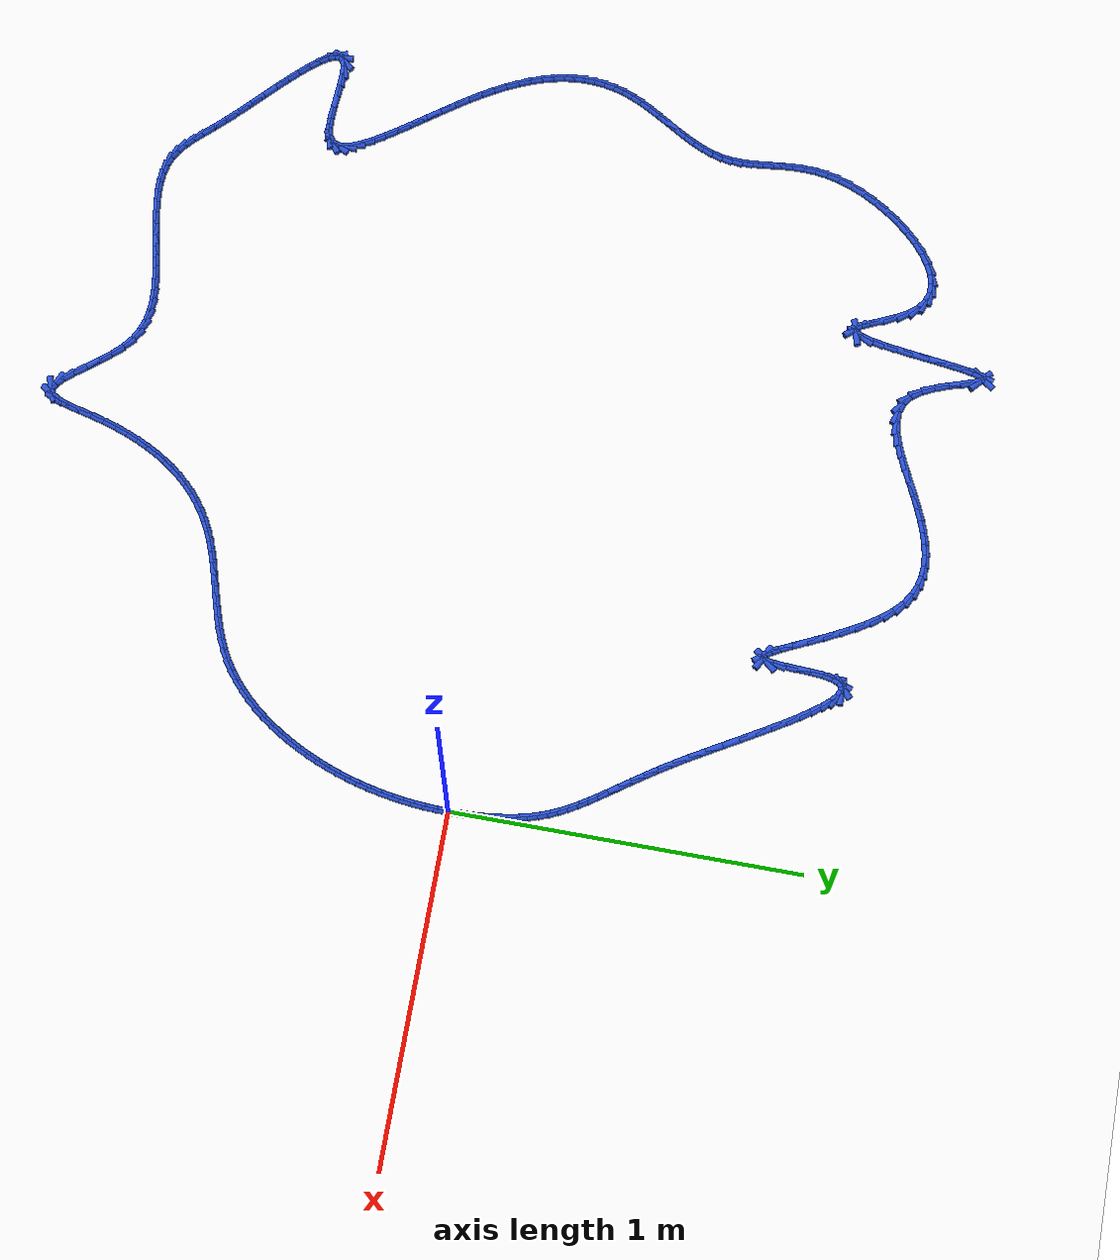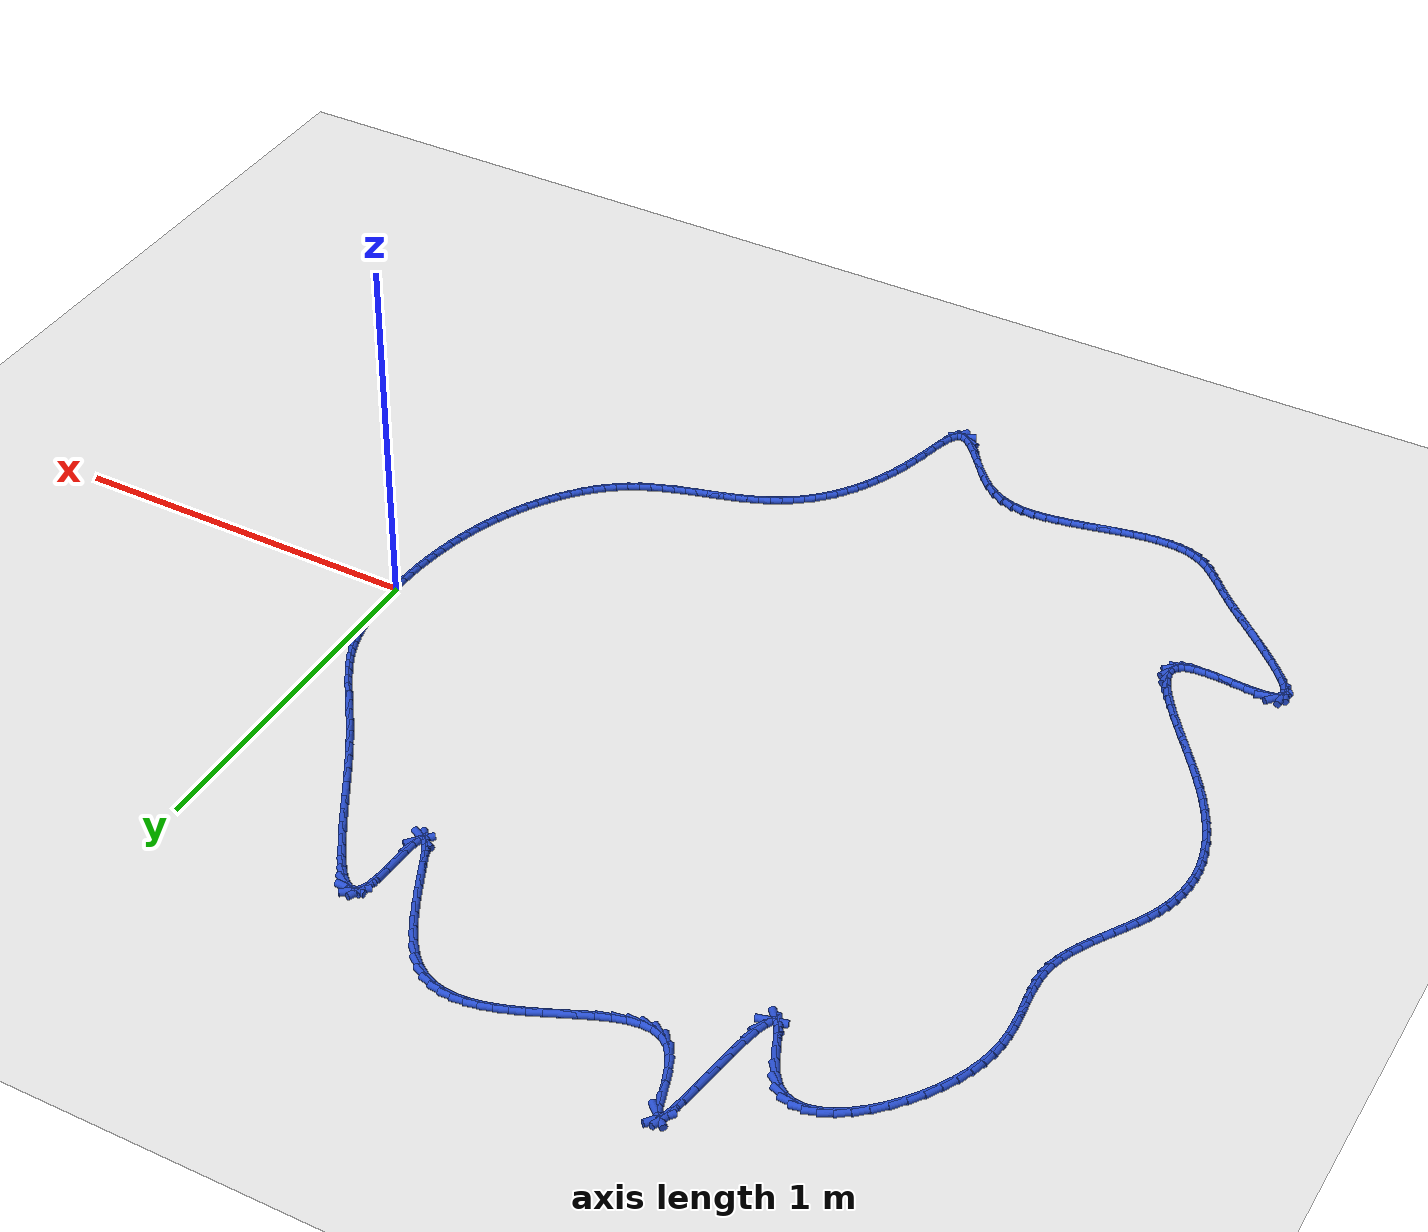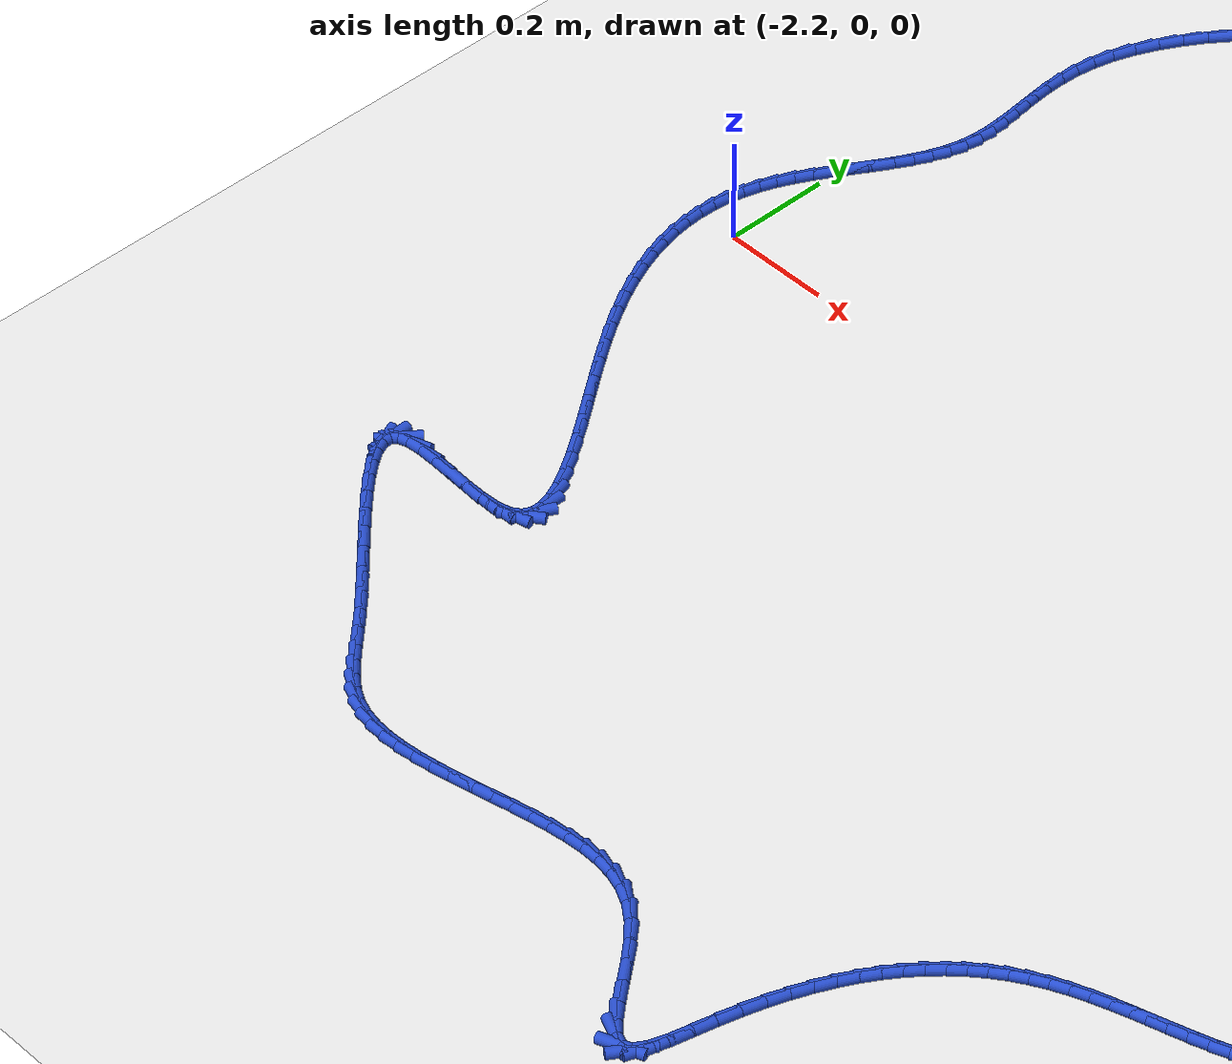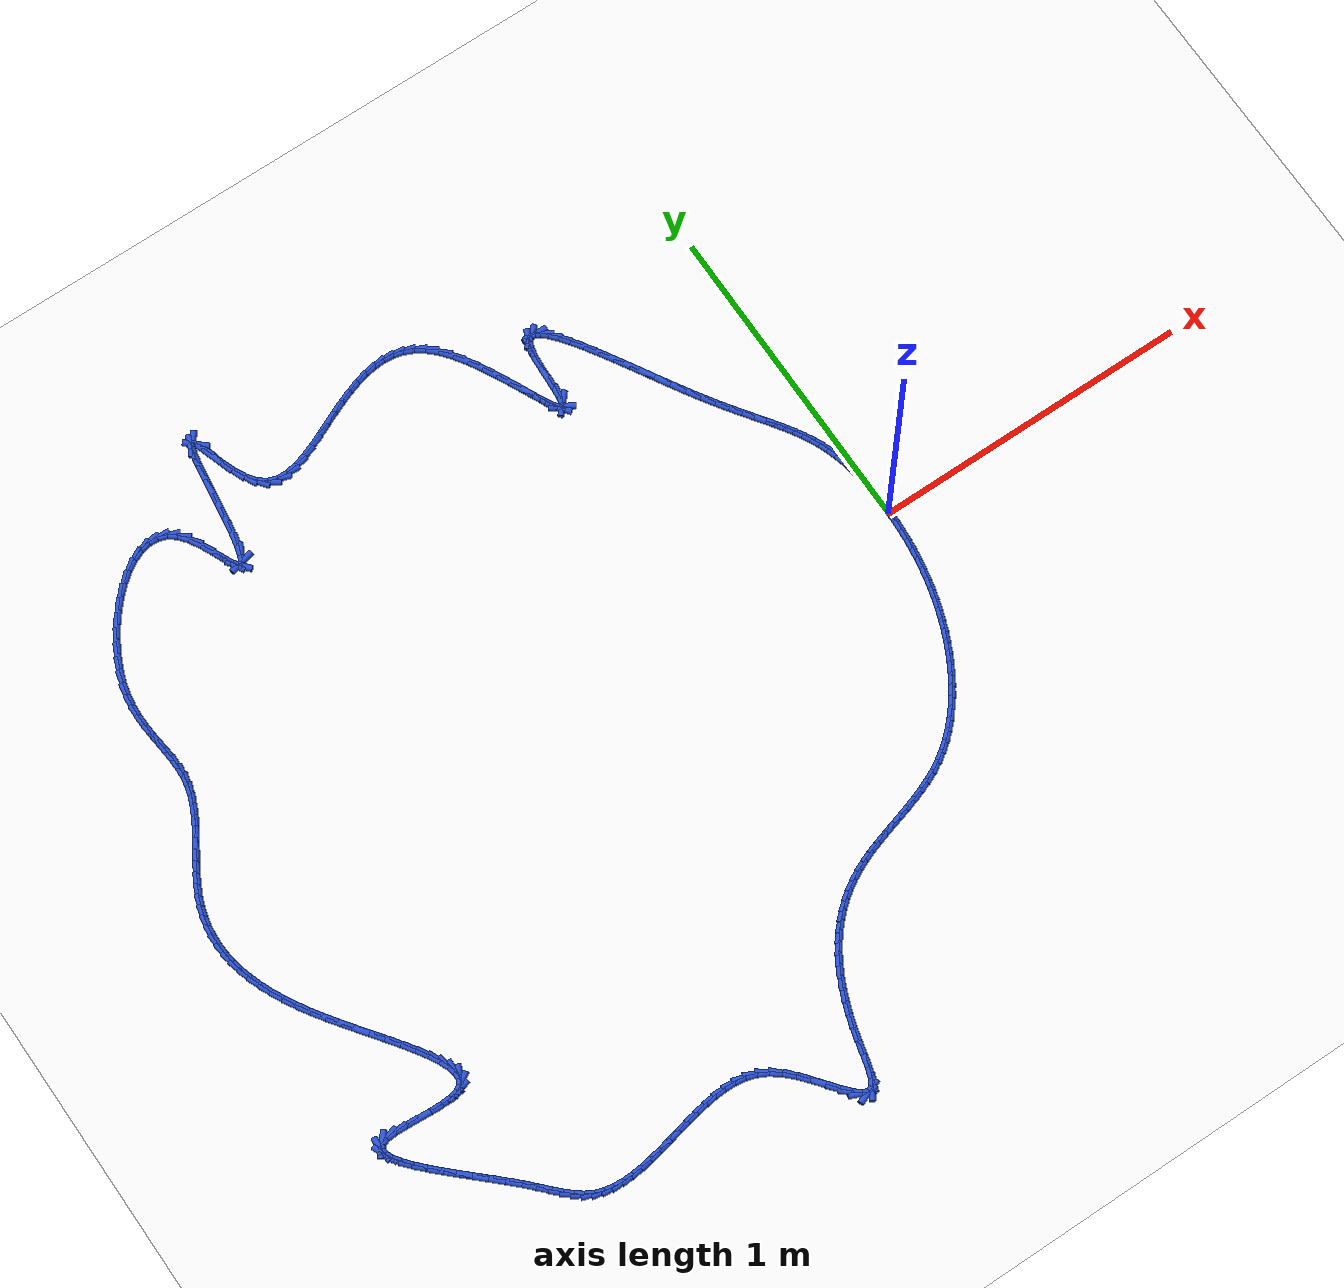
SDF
<sdf version="1.6">
 <world name="default">
  <light name="sun" type="directional">
   <pose>0 0 10 0 -0 0</pose>
   <diffuse>0.8 0.8 0.8 1</diffuse>
   <specular>0.2 0.2 0.2 1</specular>
   <attenuation>
    <range>1000</range>
    <constant>0.9</constant>
    <linear>0.01</linear>
    <quadratic>0.001</quadratic>
   </attenuation>
   <direction>-0.5 0.1 -0.9</direction>
  </light>
  <model name="ground_plane">
   <static>1</static>
   <link name="link">
    <collision name="collision">
     <geometry><plane><normal>0 0 1</normal><size>100 100</size></plane></geometry>
     <surface><friction><ode><mu>100</mu><mu2>50</mu2></ode></friction></surface>
    </collision>
    <visual name="visual">
     <cast_shadows>0</cast_shadows>
     <geometry><plane><normal>0 0 1</normal><size>100 100</size></plane></geometry>
     <material>
      <script><uri>file://media/materials/scripts/gazebo.material</uri><name>Gazebo/WhiteGlow</name></script>
     </material>
    </visual>
   </link>
  </model>
  <gravity>0 0 -9.8</gravity>
  <magnetic_field>6e-06 2.3e-05 -4.2e-05</magnetic_field>
  <atmosphere type="adiabatic"/>
  <physics name="default_physics" default="0" type="ode">
   <max_step_size>0.001</max_step_size>
   <real_time_factor>1</real_time_factor>
   <real_time_update_rate>1000</real_time_update_rate>
  </physics>
  <scene><ambient>0.4 0.4 0.4 1</ambient><background>0.7 0.7 0.7 1</background><shadows>1</shadows></scene>
  <spherical_coordinates>
   <surface_model>EARTH_WGS84</surface_model>
   <latitude_deg>0</latitude_deg>
   <longitude_deg>0</longitude_deg>
   <elevation>0</elevation>
   <heading_deg>0</heading_deg>
  </spherical_coordinates>
  <model name="line">
   <link name="link_0">
    <pose>1.8648277366750676e-17 2.0816681711721685e-17 0.01 0 1.57 -1.5640540813541342</pose>
    <collision name="collision">
     <geometry><cylinder><radius>0.01</radius><length>0.08</length></cylinder></geometry>
    </collision>
    <visual name="visual">
     <material>
      <script><name>Gazebo/Blue</name><uri>file://media/materials/scripts/gazebo.material</uri></script>
     </material>
     <geometry><cylinder><radius>0.01</radius><length>0.08</length></cylinder></geometry>
    </visual>
   </link>
   <link name="link_1">
    <pose>-0.00022728111704300744 0.03370949264959678 0.01 0 1.57 -1.5330727734446878</pose>
    <collision name="collision">
     <geometry><cylinder><radius>0.01</radius><length>0.08</length></cylinder></geometry>
    </collision>
    <visual name="visual">
     <material>
      <script><name>Gazebo/Blue</name><uri>file://media/materials/scripts/gazebo.material</uri></script>
     </material>
     <geometry><cylinder><radius>0.01</radius><length>0.08</length></cylinder></geometry>
    </visual>
   </link>
   <link name="link_2">
    <pose>-0.0015030384420562893 0.06751203752814953 0.01 0 1.57 -1.4996828587393176</pose>
    <collision name="collision">
     <geometry><cylinder><radius>0.01</radius><length>0.08</length></cylinder></geometry>
    </collision>
    <visual name="visual">
     <material>
      <script><name>Gazebo/Blue</name><uri>file://media/materials/scripts/gazebo.material</uri></script>
     </material>
     <geometry><cylinder><radius>0.01</radius><length>0.08</length></cylinder></geometry>
    </visual>
   </link>
   <link name="link_3">
    <pose>-0.0038960851850645636 0.10110639691667171 0.01 0 1.57 -1.4630347684916494</pose>
    <collision name="collision">
     <geometry><cylinder><radius>0.01</radius><length>0.08</length></cylinder></geometry>
    </collision>
    <visual name="visual">
     <material>
      <script><name>Gazebo/Blue</name><uri>file://media/materials/scripts/gazebo.material</uri></script>
     </material>
     <geometry><cylinder><radius>0.01</radius><length>0.08</length></cylinder></geometry>
    </visual>
   </link>
   <link name="link_4">
    <pose>-0.007475234556092558 0.1341913330961766 0.01 0 1.57 -1.4221208098039462</pose>
    <collision name="collision">
     <geometry><cylinder><radius>0.01</radius><length>0.08</length></cylinder></geometry>
    </collision>
    <visual name="visual">
     <material>
      <script><name>Gazebo/Blue</name><uri>file://media/materials/scripts/gazebo.material</uri></script>
     </material>
     <geometry><cylinder><radius>0.01</radius><length>0.08</length></cylinder></geometry>
    </visual>
   </link>
   <link name="link_5">
    <pose>-0.012309299765165012 0.1664656083476777 0.01 0 1.57 -1.3757061654834393</pose>
    <collision name="collision">
     <geometry><cylinder><radius>0.01</radius><length>0.08</length></cylinder></geometry>
    </collision>
    <visual name="visual">
     <material>
      <script><name>Gazebo/Blue</name><uri>file://media/materials/scripts/gazebo.material</uri></script>
     </material>
     <geometry><cylinder><radius>0.01</radius><length>0.08</length></cylinder></geometry>
    </visual>
   </link>
   <link name="link_6">
    <pose>-0.018467094022306653 0.1976279849521883 0.01 0 1.57 -1.3222450555763587</pose>
    <collision name="collision">
     <geometry><cylinder><radius>0.01</radius><length>0.08</length></cylinder></geometry>
    </collision>
    <visual name="visual">
     <material>
      <script><name>Gazebo/Blue</name><uri>file://media/materials/scripts/gazebo.material</uri></script>
     </material>
     <geometry><cylinder><radius>0.01</radius><length>0.08</length></cylinder></geometry>
    </visual>
   </link>
   <link name="link_7">
    <pose>-0.02601743053754222 0.2273772251907219 0.01 0 1.57 -1.2610309015368804</pose>
    <collision name="collision">
     <geometry><cylinder><radius>0.01</radius><length>0.08</length></cylinder></geometry>
    </collision>
    <visual name="visual">
     <material>
      <script><name>Gazebo/Blue</name><uri>file://media/materials/scripts/gazebo.material</uri></script>
     </material>
     <geometry><cylinder><radius>0.01</radius><length>0.08</length></cylinder></geometry>
    </visual>
   </link>
   <link name="link_8">
    <pose>-0.03501566513942105 0.25549065689504324 0.01 0 1.57 -1.1984716243927567</pose>
    <collision name="collision">
     <geometry><cylinder><radius>0.01</radius><length>0.08</length></cylinder></geometry>
    </collision>
    <visual name="visual">
     <material>
      <script><name>Gazebo/Blue</name><uri>file://media/materials/scripts/gazebo.material</uri></script>
     </material>
     <geometry><cylinder><radius>0.01</radius><length>0.08</length></cylinder></geometry>
    </visual>
   </link>
   <link name="link_9">
    <pose>-0.04544158082113257 0.28218680973419524 0.01 0 1.57 -1.1394189568886843</pose>
    <collision name="collision">
     <geometry><cylinder><radius>0.01</radius><length>0.08</length></cylinder></geometry>
    </collision>
    <visual name="visual">
     <material>
      <script><name>Gazebo/Blue</name><uri>file://media/materials/scripts/gazebo.material</uri></script>
     </material>
     <geometry><cylinder><radius>0.01</radius><length>0.08</length></cylinder></geometry>
    </visual>
   </link>
   <link name="link_10">
    <pose>-0.05724859883860157 0.3078381158589735 0.01 0 1.57 -1.0864862673311666</pose>
    <collision name="collision">
     <geometry><cylinder><radius>0.01</radius><length>0.08</length></cylinder></geometry>
    </collision>
    <visual name="visual">
     <material>
      <script><name>Gazebo/Blue</name><uri>file://media/materials/scripts/gazebo.material</uri></script>
     </material>
     <geometry><cylinder><radius>0.01</radius><length>0.08</length></cylinder></geometry>
    </visual>
   </link>
   <link name="link_11">
    <pose>-0.07039011322149369 0.332817166369822 0.01 0 1.57 -1.041721886535463</pose>
    <collision name="collision">
     <geometry><cylinder><radius>0.01</radius><length>0.08</length></cylinder></geometry>
    </collision>
    <visual name="visual">
     <material>
      <script><name>Gazebo/Blue</name><uri>file://media/materials/scripts/gazebo.material</uri></script>
     </material>
     <geometry><cylinder><radius>0.01</radius><length>0.08</length></cylinder></geometry>
    </visual>
   </link>
   <link name="link_12">
    <pose>-0.08481951799947454 0.3574965523671844 0.01 0 1.57 -1.0063934821426175</pose>
    <collision name="collision">
     <geometry><cylinder><radius>0.01</radius><length>0.08</length></cylinder></geometry>
    </collision>
    <visual name="visual">
     <material>
      <script><name>Gazebo/Blue</name><uri>file://media/materials/scripts/gazebo.material</uri></script>
     </material>
     <geometry><cylinder><radius>0.01</radius><length>0.08</length></cylinder></geometry>
    </visual>
   </link>
   <link name="link_13">
    <pose>-0.10049020720220972 0.38224886495150434 0.01 0 1.57 -0.980960257687894</pose>
    <collision name="collision">
     <geometry><cylinder><radius>0.01</radius><length>0.08</length></cylinder></geometry>
    </collision>
    <visual name="visual">
     <material>
      <script><name>Gazebo/Blue</name><uri>file://media/materials/scripts/gazebo.material</uri></script>
     </material>
     <geometry><cylinder><radius>0.01</radius><length>0.08</length></cylinder></geometry>
    </visual>
   </link>
   <link name="link_14">
    <pose>-0.11735557485936489 0.40744669522322585 0.01 0 1.57 -0.9651891636108009</pose>
    <collision name="collision">
     <geometry><cylinder><radius>0.01</radius><length>0.08</length></cylinder></geometry>
    </collision>
    <visual name="visual">
     <material>
      <script><name>Gazebo/Blue</name><uri>file://media/materials/scripts/gazebo.material</uri></script>
     </material>
     <geometry><cylinder><radius>0.01</radius><length>0.08</length></cylinder></geometry>
    </visual>
   </link>
   <link name="link_15">
    <pose>-0.1353690150006056 0.43346263428279236 0.01 0 1.57 -0.9583392861030646</pose>
    <collision name="collision">
     <geometry><cylinder><radius>0.01</radius><length>0.08</length></cylinder></geometry>
    </collision>
    <visual name="visual">
     <material>
      <script><name>Gazebo/Blue</name><uri>file://media/materials/scripts/gazebo.material</uri></script>
     </material>
     <geometry><cylinder><radius>0.01</radius><length>0.08</length></cylinder></geometry>
    </visual>
   </link>
   <link name="link_16">
    <pose>-0.15448392165559754 0.46066927323064777 0.01 0 1.57 -0.959351847053833</pose>
    <collision name="collision">
     <geometry><cylinder><radius>0.01</radius><length>0.08</length></cylinder></geometry>
    </collision>
    <visual name="visual">
     <material>
      <script><name>Gazebo/Blue</name><uri>file://media/materials/scripts/gazebo.material</uri></script>
     </material>
     <geometry><cylinder><radius>0.01</radius><length>0.08</length></cylinder></geometry>
    </visual>
   </link>
   <link name="link_17">
    <pose>-0.17465368885400634 0.4894392031672359 0.01 0 1.57 -0.9670116891092768</pose>
    <collision name="collision">
     <geometry><cylinder><radius>0.01</radius><length>0.08</length></cylinder></geometry>
    </collision>
    <visual name="visual">
     <material>
      <script><name>Gazebo/Blue</name><uri>file://media/materials/scripts/gazebo.material</uri></script>
     </material>
     <geometry><cylinder><radius>0.01</radius><length>0.08</length></cylinder></geometry>
    </visual>
   </link>
   <link name="link_18">
    <pose>-0.19583171062549742 0.520145015193 0.01 0 1.57 -0.980069513488421</pose>
    <collision name="collision">
     <geometry><cylinder><radius>0.01</radius><length>0.08</length></cylinder></geometry>
    </collision>
    <visual name="visual">
     <material>
      <script><name>Gazebo/Blue</name><uri>file://media/materials/scripts/gazebo.material</uri></script>
     </material>
     <geometry><cylinder><radius>0.01</radius><length>0.08</length></cylinder></geometry>
    </visual>
   </link>
   <link name="link_19">
    <pose>-0.21797138099973667 0.5531593004083847 0.01 0 1.57 -0.9973268107151732</pose>
    <collision name="collision">
     <geometry><cylinder><radius>0.01</radius><length>0.08</length></cylinder></geometry>
    </collision>
    <visual name="visual">
     <material>
      <script><name>Gazebo/Blue</name><uri>file://media/materials/scripts/gazebo.material</uri></script>
     </material>
     <geometry><cylinder><radius>0.01</radius><length>0.08</length></cylinder></geometry>
    </visual>
   </link>
   <link name="link_20">
    <pose>-0.24102609400638947 0.5888546499138331 0.01 0 1.57 -1.0170251952043114</pose>
    <collision name="collision">
     <geometry><cylinder><radius>0.01</radius><length>0.08</length></cylinder></geometry>
    </collision>
    <visual name="visual">
     <material>
      <script><name>Gazebo/Blue</name><uri>file://media/materials/scripts/gazebo.material</uri></script>
     </material>
     <geometry><cylinder><radius>0.01</radius><length>0.08</length></cylinder></geometry>
    </visual>
   </link>
   <link name="link_21">
    <pose>-0.264937218835737 0.6275266449607853 0.01 0 1.57 -1.0324751283271645</pose>
    <collision name="collision">
     <geometry><cylinder><radius>0.01</radius><length>0.08</length></cylinder></geometry>
    </collision>
    <visual name="visual">
     <material>
      <script><name>Gazebo/Blue</name><uri>file://media/materials/scripts/gazebo.material</uri></script>
     </material>
     <geometry><cylinder><radius>0.01</radius><length>0.08</length></cylinder></geometry>
    </visual>
   </link>
   <link name="link_22">
    <pose>-0.2895264194555888 0.6687042469055947 0.01 0 1.57 -1.0415076142069588</pose>
    <collision name="collision">
     <geometry><cylinder><radius>0.01</radius><length>0.08</length></cylinder></geometry>
    </collision>
    <visual name="visual">
     <material>
      <script><name>Gazebo/Blue</name><uri>file://media/materials/scripts/gazebo.material</uri></script>
     </material>
     <geometry><cylinder><radius>0.01</radius><length>0.08</length></cylinder></geometry>
    </visual>
   </link>
   <link name="link_23">
    <pose>-0.3145467077563362 0.7114767533430729 0.01 0 1.57 -1.045183147144786</pose>
    <collision name="collision">
     <geometry><cylinder><radius>0.01</radius><length>0.08</length></cylinder></geometry>
    </collision>
    <visual name="visual">
     <material>
      <script><name>Gazebo/Blue</name><uri>file://media/materials/scripts/gazebo.material</uri></script>
     </material>
     <geometry><cylinder><radius>0.01</radius><length>0.08</length></cylinder></geometry>
    </visual>
   </link>
   <link name="link_24">
    <pose>-0.3397502816486447 0.7549282489538472 0.01 0 1.57 -1.043921646903295</pose>
    <collision name="collision">
     <geometry><cylinder><radius>0.01</radius><length>0.08</length></cylinder></geometry>
    </collision>
    <visual name="visual">
     <material>
      <script><name>Gazebo/Blue</name><uri>file://media/materials/scripts/gazebo.material</uri></script>
     </material>
     <geometry><cylinder><radius>0.01</radius><length>0.08</length></cylinder></geometry>
    </visual>
   </link>
   <link name="link_25">
    <pose>-0.364889339043179 0.7981428184185431 0.01 0 1.57 -1.0375802490978816</pose>
    <collision name="collision">
     <geometry><cylinder><radius>0.01</radius><length>0.08</length></cylinder></geometry>
    </collision>
    <visual name="visual">
     <material>
      <script><name>Gazebo/Blue</name><uri>file://media/materials/scripts/gazebo.material</uri></script>
     </material>
     <geometry><cylinder><radius>0.01</radius><length>0.08</length></cylinder></geometry>
    </visual>
   </link>
   <link name="link_26">
    <pose>-0.3897160778506043 0.8402045464177872 0.01 0 1.57 -1.0254122331068831</pose>
    <collision name="collision">
     <geometry><cylinder><radius>0.01</radius><length>0.08</length></cylinder></geometry>
    </collision>
    <visual name="visual">
     <material>
      <script><name>Gazebo/Blue</name><uri>file://media/materials/scripts/gazebo.material</uri></script>
     </material>
     <geometry><cylinder><radius>0.01</radius><length>0.08</length></cylinder></geometry>
    </visual>
   </link>
   <link name="link_27">
    <pose>-0.41398269598158627 0.8801975176322065 0.01 0 1.57 -1.0058392777826617</pose>
    <collision name="collision">
     <geometry><cylinder><radius>0.01</radius><length>0.08</length></cylinder></geometry>
    </collision>
    <visual name="visual">
     <material>
      <script><name>Gazebo/Blue</name><uri>file://media/materials/scripts/gazebo.material</uri></script>
     </material>
     <geometry><cylinder><radius>0.01</radius><length>0.08</length></cylinder></geometry>
    </visual>
   </link>
   <link name="link_28">
    <pose>-0.4374413913467897 0.9172058167424274 0.01 0 1.57 -0.9759007877650887</pose>
    <collision name="collision">
     <geometry><cylinder><radius>0.01</radius><length>0.08</length></cylinder></geometry>
    </collision>
    <visual name="visual">
     <material>
      <script><name>Gazebo/Blue</name><uri>file://media/materials/scripts/gazebo.material</uri></script>
     </material>
     <geometry><cylinder><radius>0.01</radius><length>0.08</length></cylinder></geometry>
    </visual>
   </link>
   <link name="link_29">
    <pose>-0.4598443618568799 0.9503135284290759 0.01 0 1.57 -0.9299918227641704</pose>
    <collision name="collision">
     <geometry><cylinder><radius>0.01</radius><length>0.08</length></cylinder></geometry>
    </collision>
    <visual name="visual">
     <material>
      <script><name>Gazebo/Blue</name><uri>file://media/materials/scripts/gazebo.material</uri></script>
     </material>
     <geometry><cylinder><radius>0.01</radius><length>0.08</length></cylinder></geometry>
    </visual>
   </link>
   <link name="link_30">
    <pose>-0.4809438054225219 0.9786047373727785 0.01 0 1.57 -0.8567774643884406</pose>
    <collision name="collision">
     <geometry><cylinder><radius>0.01</radius><length>0.08</length></cylinder></geometry>
    </collision>
    <visual name="visual">
     <material>
      <script><name>Gazebo/Blue</name><uri>file://media/materials/scripts/gazebo.material</uri></script>
     </material>
     <geometry><cylinder><radius>0.01</radius><length>0.08</length></cylinder></geometry>
    </visual>
   </link>
   <link name="link_31">
    <pose>-0.500491919954381 1.0011635282541622 0.01 0 1.57 -0.7308309836425345</pose>
    <collision name="collision">
     <geometry><cylinder><radius>0.01</radius><length>0.08</length></cylinder></geometry>
    </collision>
    <visual name="visual">
     <material>
      <script><name>Gazebo/Blue</name><uri>file://media/materials/scripts/gazebo.material</uri></script>
     </material>
     <geometry><cylinder><radius>0.01</radius><length>0.08</length></cylinder></geometry>
    </visual>
   </link>
   <link name="link_32">
    <pose>-0.5182409033631223 1.0170739857538527 0.01 0 1.57 -0.4885571650840036</pose>
    <collision name="collision">
     <geometry><cylinder><radius>0.01</radius><length>0.08</length></cylinder></geometry>
    </collision>
    <visual name="visual">
     <material>
      <script><name>Gazebo/Blue</name><uri>file://media/materials/scripts/gazebo.material</uri></script>
     </material>
     <geometry><cylinder><radius>0.01</radius><length>0.08</length></cylinder></geometry>
    </visual>
   </link>
   <link name="link_33">
    <pose>-0.5339429535594112 1.0254201945524772 0.01 0 1.57 0.009990871834794399</pose>
    <collision name="collision">
     <geometry><cylinder><radius>0.01</radius><length>0.08</length></cylinder></geometry>
    </collision>
    <visual name="visual">
     <material>
      <script><name>Gazebo/Blue</name><uri>file://media/materials/scripts/gazebo.material</uri></script>
     </material>
     <geometry><cylinder><radius>0.01</radius><length>0.08</length></cylinder></geometry>
    </visual>
   </link>
   <link name="link_34">
    <pose>-0.5473502684539124 1.0252862393306619 0.01 0 1.57 0.7200461406600918</pose>
    <collision name="collision">
     <geometry><cylinder><radius>0.01</radius><length>0.08</length></cylinder></geometry>
    </collision>
    <visual name="visual">
     <material>
      <script><name>Gazebo/Blue</name><uri>file://media/materials/scripts/gazebo.material</uri></script>
     </material>
     <geometry><cylinder><radius>0.01</radius><length>0.08</length></cylinder></geometry>
    </visual>
   </link>
   <link name="link_35">
    <pose>-0.5582150459572917 1.0157562047690334 0.01 0 1.57 1.1843040212507043</pose>
    <collision name="collision">
     <geometry><cylinder><radius>0.01</radius><length>0.08</length></cylinder></geometry>
    </collision>
    <visual name="visual">
     <material>
      <script><name>Gazebo/Blue</name><uri>file://media/materials/scripts/gazebo.material</uri></script>
     </material>
     <geometry><cylinder><radius>0.01</radius><length>0.08</length></cylinder></geometry>
    </visual>
   </link>
   <link name="link_36">
    <pose>-0.5662896560022819 0.9959149388131334 0.01 0 1.57 1.3959791009258045</pose>
    <collision name="collision">
     <geometry><cylinder><radius>0.01</radius><length>0.08</length></cylinder></geometry>
    </collision>
    <visual name="visual">
     <material>
      <script><name>Gazebo/Blue</name><uri>file://media/materials/scripts/gazebo.material</uri></script>
     </material>
     <geometry><cylinder><radius>0.01</radius><length>0.08</length></cylinder></geometry>
    </visual>
   </link>
   <link name="link_37">
    <pose>-0.5715789596082179 0.9659675967618204 0.01 0 1.57 1.4814861734477431</pose>
    <collision name="collision">
     <geometry><cylinder><radius>0.01</radius><length>0.08</length></cylinder></geometry>
    </collision>
    <visual name="visual">
     <material>
      <script><name>Gazebo/Blue</name><uri>file://media/materials/scripts/gazebo.material</uri></script>
     </material>
     <geometry><cylinder><radius>0.01</radius><length>0.08</length></cylinder></geometry>
    </visual>
   </link>
   <link name="link_38">
    <pose>-0.5748460427660054 0.9294835913321247 0.01 0 1.57 1.5154804421000168</pose>
    <collision name="collision">
     <geometry><cylinder><radius>0.01</radius><length>0.08</length></cylinder></geometry>
    </collision>
    <visual name="visual">
     <material>
      <script><name>Gazebo/Blue</name><uri>file://media/materials/scripts/gazebo.material</uri></script>
     </material>
     <geometry><cylinder><radius>0.01</radius><length>0.08</length></cylinder></geometry>
    </visual>
   </link>
   <link name="link_39">
    <pose>-0.5769957291643972 0.8906612278775544 0.01 0 1.57 1.518436579236036</pose>
    <collision name="collision">
     <geometry><cylinder><radius>0.01</radius><length>0.08</length></cylinder></geometry>
    </collision>
    <visual name="visual">
     <material>
      <script><name>Gazebo/Blue</name><uri>file://media/materials/scripts/gazebo.material</uri></script>
     </material>
     <geometry><cylinder><radius>0.01</radius><length>0.08</length></cylinder></geometry>
    </visual>
   </link>
   <link name="link_40">
    <pose>-0.5789328424921457 0.8536988117516164 0.01 0 1.57 1.4859195148842421</pose>
    <collision name="collision">
     <geometry><cylinder><radius>0.01</radius><length>0.08</length></cylinder></geometry>
    </collision>
    <visual name="visual">
     <material>
      <script><name>Gazebo/Blue</name><uri>file://media/materials/scripts/gazebo.material</uri></script>
     </material>
     <geometry><cylinder><radius>0.01</radius><length>0.08</length></cylinder></geometry>
    </visual>
   </link>
   <link name="link_41">
    <pose>-0.5815622064380038 0.8227946483078182 0.01 0 1.57 1.3689119356502872</pose>
    <collision name="collision">
     <geometry><cylinder><radius>0.01</radius><length>0.08</length></cylinder></geometry>
    </collision>
    <visual name="visual">
     <material>
      <script><name>Gazebo/Blue</name><uri>file://media/materials/scripts/gazebo.material</uri></script>
     </material>
     <geometry><cylinder><radius>0.01</radius><length>0.08</length></cylinder></geometry>
    </visual>
   </link>
   <link name="link_42">
    <pose>-0.5857884452191734 0.8021458728621471 0.01 0 1.57 0.8580099437129778</pose>
    <collision name="collision">
     <geometry><cylinder><radius>0.01</radius><length>0.08</length></cylinder></geometry>
    </collision>
    <visual name="visual">
     <material>
      <script><name>Gazebo/Blue</name><uri>file://media/materials/scripts/gazebo.material</uri></script>
     </material>
     <geometry><cylinder><radius>0.01</radius><length>0.08</length></cylinder></geometry>
    </visual>
   </link>
   <link name="link_43">
    <pose>-0.5922901960859644 0.7946240520996425 0.01 0 1.57 -0.4823884685321903</pose>
    <collision name="collision">
     <geometry><cylinder><radius>0.01</radius><length>0.08</length></cylinder></geometry>
    </collision>
    <visual name="visual">
     <material>
      <script><name>Gazebo/Blue</name><uri>file://media/materials/scripts/gazebo.material</uri></script>
     </material>
     <geometry><cylinder><radius>0.01</radius><length>0.08</length></cylinder></geometry>
    </visual>
   </link>
   <link name="link_44">
    <pose>-0.601086214118704 0.799230090973471 0.01 0 1.57 -0.93953289880586</pose>
    <collision name="collision">
     <geometry><cylinder><radius>0.01</radius><length>0.08</length></cylinder></geometry>
    </collision>
    <visual name="visual">
     <material>
      <script><name>Gazebo/Blue</name><uri>file://media/materials/scripts/gazebo.material</uri></script>
     </material>
     <geometry><cylinder><radius>0.01</radius><length>0.08</length></cylinder></geometry>
    </visual>
   </link>
   <link name="link_45">
    <pose>-0.6120754555692078 0.8142621921027499 0.01 0 1.57 -1.0674549173226022</pose>
    <collision name="collision">
     <geometry><cylinder><radius>0.01</radius><length>0.08</length></cylinder></geometry>
    </collision>
    <visual name="visual">
     <material>
      <script><name>Gazebo/Blue</name><uri>file://media/materials/scripts/gazebo.material</uri></script>
     </material>
     <geometry><cylinder><radius>0.01</radius><length>0.08</length></cylinder></geometry>
    </visual>
   </link>
   <link name="link_46">
    <pose>-0.6251568766892915 0.8380185581065956 0.01 0 1.57 -1.1154183656569396</pose>
    <collision name="collision">
     <geometry><cylinder><radius>0.01</radius><length>0.08</length></cylinder></geometry>
    </collision>
    <visual name="visual">
     <material>
      <script><name>Gazebo/Blue</name><uri>file://media/materials/scripts/gazebo.material</uri></script>
     </material>
     <geometry><cylinder><radius>0.01</radius><length>0.08</length></cylinder></geometry>
    </visual>
   </link>
   <link name="link_47">
    <pose>-0.6402294337307702 0.8687973916041248 0.01 0 1.57 -1.131528865879488</pose>
    <collision name="collision">
     <geometry><cylinder><radius>0.01</radius><length>0.08</length></cylinder></geometry>
    </collision>
    <visual name="visual">
     <material>
      <script><name>Gazebo/Blue</name><uri>file://media/materials/scripts/gazebo.material</uri></script>
     </material>
     <geometry><cylinder><radius>0.01</radius><length>0.08</length></cylinder></geometry>
    </visual>
   </link>
   <link name="link_48">
    <pose>-0.6571920829454594 0.9048968952144543 0.01 0 1.57 -1.1297033609013452</pose>
    <collision name="collision">
     <geometry><cylinder><radius>0.01</radius><length>0.08</length></cylinder></geometry>
    </collision>
    <visual name="visual">
     <material>
      <script><name>Gazebo/Blue</name><uri>file://media/materials/scripts/gazebo.material</uri></script>
     </material>
     <geometry><cylinder><radius>0.01</radius><length>0.08</length></cylinder></geometry>
    </visual>
   </link>
   <link name="link_49">
    <pose>-0.6759437805851745 0.9446152715567006 0.01 0 1.57 -1.1144385572703608</pose>
    <collision name="collision">
     <geometry><cylinder><radius>0.01</radius><length>0.08</length></cylinder></geometry>
    </collision>
    <visual name="visual">
     <material>
      <script><name>Gazebo/Blue</name><uri>file://media/materials/scripts/gazebo.material</uri></script>
     </material>
     <geometry><cylinder><radius>0.01</radius><length>0.08</length></cylinder></geometry>
    </visual>
   </link>
   <link name="link_50">
    <pose>-0.6963834829017308 0.9862507232499802 0.01 0 1.57 -1.0863190821722675</pose>
    <collision name="collision">
     <geometry><cylinder><radius>0.01</radius><length>0.08</length></cylinder></geometry>
    </collision>
    <visual name="visual">
     <material>
      <script><name>Gazebo/Blue</name><uri>file://media/materials/scripts/gazebo.material</uri></script>
     </material>
     <geometry><cylinder><radius>0.01</radius><length>0.08</length></cylinder></geometry>
    </visual>
   </link>
   <link name="link_51">
    <pose>-0.7184101461469438 1.0281014529134096 0.01 0 1.57 -1.0433359493110503</pose>
    <collision name="collision">
     <geometry><cylinder><radius>0.01</radius><length>0.08</length></cylinder></geometry>
    </collision>
    <visual name="visual">
     <material>
      <script><name>Gazebo/Blue</name><uri>file://media/materials/scripts/gazebo.material</uri></script>
     </material>
     <geometry><cylinder><radius>0.01</radius><length>0.08</length></cylinder></geometry>
    </visual>
   </link>
   <link name="link_52">
    <pose>-0.7419227265726289 1.0684656631661062 0.01 0 1.57 -0.9806825858684807</pose>
    <collision name="collision">
     <geometry><cylinder><radius>0.01</radius><length>0.08</length></cylinder></geometry>
    </collision>
    <visual name="visual">
     <material>
      <script><name>Gazebo/Blue</name><uri>file://media/materials/scripts/gazebo.material</uri></script>
     </material>
     <geometry><cylinder><radius>0.01</radius><length>0.08</length></cylinder></geometry>
    </visual>
   </link>
   <link name="link_53">
    <pose>-0.7668201804306017 1.1056415566271864 0.01 0 1.57 -0.8894303683942326</pose>
    <collision name="collision">
     <geometry><cylinder><radius>0.01</radius><length>0.08</length></cylinder></geometry>
    </collision>
    <visual name="visual">
     <material>
      <script><name>Gazebo/Blue</name><uri>file://media/materials/scripts/gazebo.material</uri></script>
     </material>
     <geometry><cylinder><radius>0.01</radius><length>0.08</length></cylinder></geometry>
    </visual>
   </link>
   <link name="link_54">
    <pose>-0.7930014639726775 1.1379273359157664 0.01 0 1.57 -0.7563948264282714</pose>
    <collision name="collision">
     <geometry><cylinder><radius>0.01</radius><length>0.08</length></cylinder></geometry>
    </collision>
    <visual name="visual">
     <material>
      <script><name>Gazebo/Blue</name><uri>file://media/materials/scripts/gazebo.material</uri></script>
     </material>
     <geometry><cylinder><radius>0.01</radius><length>0.08</length></cylinder></geometry>
    </visual>
   </link>
   <link name="link_55">
    <pose>-0.8203677303846755 1.163750498682871 0.01 0 1.57 -0.5914955888662017</pose>
    <collision name="collision">
     <geometry><cylinder><radius>0.01</radius><length>0.08</length></cylinder></geometry>
    </collision>
    <visual name="visual">
     <material>
      <script><name>Gazebo/Blue</name><uri>file://media/materials/scripts/gazebo.material</uri></script>
     </material>
     <geometry><cylinder><radius>0.01</radius><length>0.08</length></cylinder></geometry>
    </visual>
   </link>
   <link name="link_56">
    <pose>-0.8488428914824494 1.1828779445785118 0.01 0 1.57 -0.4145488062492456</pose>
    <collision name="collision">
     <geometry><cylinder><radius>0.01</radius><length>0.08</length></cylinder></geometry>
    </collision>
    <visual name="visual">
     <material>
      <script><name>Gazebo/Blue</name><uri>file://media/materials/scripts/gazebo.material</uri></script>
     </material>
     <geometry><cylinder><radius>0.01</radius><length>0.08</length></cylinder></geometry>
    </visual>
   </link>
   <link name="link_57">
    <pose>-0.8783643211797995 1.1958688512093798 0.01 0 1.57 -0.23872295142183042</pose>
    <collision name="collision">
     <geometry><cylinder><radius>0.01</radius><length>0.08</length></cylinder></geometry>
    </collision>
    <visual name="visual">
     <material>
      <script><name>Gazebo/Blue</name><uri>file://media/materials/scripts/gazebo.material</uri></script>
     </material>
     <geometry><cylinder><radius>0.01</radius><length>0.08</length></cylinder></geometry>
    </visual>
   </link>
   <link name="link_58">
    <pose>-0.9088695687757763 1.2032927180404345 0.01 0 1.57 -0.07705324757670078</pose>
    <collision name="collision">
     <geometry><cylinder><radius>0.01</radius><length>0.08</length></cylinder></geometry>
    </collision>
    <visual name="visual">
     <material>
      <script><name>Gazebo/Blue</name><uri>file://media/materials/scripts/gazebo.material</uri></script>
     </material>
     <geometry><cylinder><radius>0.01</radius><length>0.08</length></cylinder></geometry>
    </visual>
   </link>
   <link name="link_59">
    <pose>-0.9402961835694289 1.2057190445366324 0.01 0 1.57 0.06192109284528416</pose>
    <collision name="collision">
     <geometry><cylinder><radius>0.01</radius><length>0.08</length></cylinder></geometry>
    </collision>
    <visual name="visual">
     <material>
      <script><name>Gazebo/Blue</name><uri>file://media/materials/scripts/gazebo.material</uri></script>
     </material>
     <geometry><cylinder><radius>0.01</radius><length>0.08</length></cylinder></geometry>
    </visual>
   </link>
   <link name="link_60">
    <pose>-0.9725817148598082 1.203717330162931 0.01 0 1.57 0.17532456697047252</pose>
    <collision name="collision">
     <geometry><cylinder><radius>0.01</radius><length>0.08</length></cylinder></geometry>
    </collision>
    <visual name="visual">
     <material>
      <script><name>Gazebo/Blue</name><uri>file://media/materials/scripts/gazebo.material</uri></script>
     </material>
     <geometry><cylinder><radius>0.01</radius><length>0.08</length></cylinder></geometry>
    </visual>
   </link>
   <link name="link_61">
    <pose>-1.005663711945963 1.1978570743842876 0.01 0 1.57 0.264234743004453</pose>
    <collision name="collision">
     <geometry><cylinder><radius>0.01</radius><length>0.08</length></cylinder></geometry>
    </collision>
    <visual name="visual">
     <material>
      <script><name>Gazebo/Blue</name><uri>file://media/materials/scripts/gazebo.material</uri></script>
     </material>
     <geometry><cylinder><radius>0.01</radius><length>0.08</length></cylinder></geometry>
    </visual>
   </link>
   <link name="link_62">
    <pose>-1.0394797241269431 1.1887077766656597 0.01 0 1.57 0.3314522249867367</pose>
    <collision name="collision">
     <geometry><cylinder><radius>0.01</radius><length>0.08</length></cylinder></geometry>
    </collision>
    <visual name="visual">
     <material>
      <script><name>Gazebo/Blue</name><uri>file://media/materials/scripts/gazebo.material</uri></script>
     </material>
     <geometry><cylinder><radius>0.01</radius><length>0.08</length></cylinder></geometry>
    </visual>
   </link>
   <link name="link_63">
    <pose>-1.0739673007017994 1.1768389364720049 0.01 0 1.57 0.38002011572774397</pose>
    <collision name="collision">
     <geometry><cylinder><radius>0.01</radius><length>0.08</length></cylinder></geometry>
    </collision>
    <visual name="visual">
     <material>
      <script><name>Gazebo/Blue</name><uri>file://media/materials/scripts/gazebo.material</uri></script>
     </material>
     <geometry><cylinder><radius>0.01</radius><length>0.08</length></cylinder></geometry>
    </visual>
   </link>
   <link name="link_64">
    <pose>-1.1090639909695805 1.1628200532682806 0.01 0 1.57 0.4125390015599552</pose>
    <collision name="collision">
     <geometry><cylinder><radius>0.01</radius><length>0.08</length></cylinder></geometry>
    </collision>
    <visual name="visual">
     <material>
      <script><name>Gazebo/Blue</name><uri>file://media/materials/scripts/gazebo.material</uri></script>
     </material>
     <geometry><cylinder><radius>0.01</radius><length>0.08</length></cylinder></geometry>
    </visual>
   </link>
   <link name="link_65">
    <pose>-1.144707344229337 1.1472206265194442 0.01 0 1.57 0.43095117782811987</pose>
    <collision name="collision">
     <geometry><cylinder><radius>0.01</radius><length>0.08</length></cylinder></geometry>
    </collision>
    <visual name="visual">
     <material>
      <script><name>Gazebo/Blue</name><uri>file://media/materials/scripts/gazebo.material</uri></script>
     </material>
     <geometry><cylinder><radius>0.01</radius><length>0.08</length></cylinder></geometry>
    </visual>
   </link>
   <link name="link_66">
    <pose>-1.180834909780119 1.130610155690453 0.01 0 1.57 0.4360113877469931</pose>
    <collision name="collision">
     <geometry><cylinder><radius>0.01</radius><length>0.08</length></cylinder></geometry>
    </collision>
    <visual name="visual">
     <material>
      <script><name>Gazebo/Blue</name><uri>file://media/materials/scripts/gazebo.material</uri></script>
     </material>
     <geometry><cylinder><radius>0.01</radius><length>0.08</length></cylinder></geometry>
    </visual>
   </link>
   <link name="link_67">
    <pose>-1.217366739569725 1.1135893548414888 0.01 0 1.57 0.4201901136541147</pose>
    <collision name="collision">
     <geometry><cylinder><radius>0.01</radius><length>0.08</length></cylinder></geometry>
    </collision>
    <visual name="visual">
     <material>
      <script><name>Gazebo/Blue</name><uri>file://media/materials/scripts/gazebo.material</uri></script>
     </material>
     <geometry><cylinder><radius>0.01</radius><length>0.08</length></cylinder></geometry>
    </visual>
   </link>
   <link name="link_68">
    <pose>-1.2539513632373998 1.0972433232882244 0.01 0 1.57 0.37512915570288063</pose>
    <collision name="collision">
     <geometry><cylinder><radius>0.01</radius><length>0.08</length></cylinder></geometry>
    </collision>
    <visual name="visual">
     <material>
      <script><name>Gazebo/Blue</name><uri>file://media/materials/scripts/gazebo.material</uri></script>
     </material>
     <geometry><cylinder><radius>0.01</radius><length>0.08</length></cylinder></geometry>
    </visual>
   </link>
   <link name="link_69">
    <pose>-1.290023211756222 1.083039104053508 0.01 0 1.57 0.29378081700761033</pose>
    <collision name="collision">
     <geometry><cylinder><radius>0.01</radius><length>0.08</length></cylinder></geometry>
    </collision>
    <visual name="visual">
     <material>
      <script><name>Gazebo/Blue</name><uri>file://media/materials/scripts/gazebo.material</uri></script>
     </material>
     <geometry><cylinder><radius>0.01</radius><length>0.08</length></cylinder></geometry>
    </visual>
   </link>
   <link name="link_70">
    <pose>-1.3250109071169014 1.0724541031591772 0.01 0 1.57 0.16319276041672318</pose>
    <collision name="collision">
     <geometry><cylinder><radius>0.01</radius><length>0.08</length></cylinder></geometry>
    </collision>
    <visual name="visual">
     <material>
      <script><name>Gazebo/Blue</name><uri>file://media/materials/scripts/gazebo.material</uri></script>
     </material>
     <geometry><cylinder><radius>0.01</radius><length>0.08</length></cylinder></geometry>
    </visual>
   </link>
   <link name="link_71">
    <pose>-1.3583430713101499 1.0669657266270685 0.01 0 1.57 -0.03488842412305928</pose>
    <collision name="collision">
     <geometry><cylinder><radius>0.01</radius><length>0.08</length></cylinder></geometry>
    </collision>
    <visual name="visual">
     <material>
      <script><name>Gazebo/Blue</name><uri>file://media/materials/scripts/gazebo.material</uri></script>
     </material>
     <geometry><cylinder><radius>0.01</radius><length>0.08</length></cylinder></geometry>
    </visual>
   </link>
   <link name="link_72">
    <pose>-1.389448326326677 1.068051380479019 0.01 0 1.57 -0.31222802528877996</pose>
    <collision name="collision">
     <geometry><cylinder><radius>0.01</radius><length>0.08</length></cylinder></geometry>
    </collision>
    <visual name="visual">
     <material>
      <script><name>Gazebo/Blue</name><uri>file://media/materials/scripts/gazebo.material</uri></script>
     </material>
     <geometry><cylinder><radius>0.01</radius><length>0.08</length></cylinder></geometry>
    </visual>
   </link>
   <link name="link_73">
    <pose>-1.4177552941571925 1.0771884707368655 0.01 0 1.57 -0.6425497125516809</pose>
    <collision name="collision">
     <geometry><cylinder><radius>0.01</radius><length>0.08</length></cylinder></geometry>
    </collision>
    <visual name="visual">
     <material>
      <script><name>Gazebo/Blue</name><uri>file://media/materials/scripts/gazebo.material</uri></script>
     </material>
     <geometry><cylinder><radius>0.01</radius><length>0.08</length></cylinder></geometry>
    </visual>
   </link>
   <link name="link_74">
    <pose>-1.4426925967924078 1.095854403422445 0.01 0 1.57 -0.9385215925162576</pose>
    <collision name="collision">
     <geometry><cylinder><radius>0.01</radius><length>0.08</length></cylinder></geometry>
    </collision>
    <visual name="visual">
     <material>
      <script><name>Gazebo/Blue</name><uri>file://media/materials/scripts/gazebo.material</uri></script>
     </material>
     <geometry><cylinder><radius>0.01</radius><length>0.08</length></cylinder></geometry>
    </visual>
   </link>
   <link name="link_75">
    <pose>-1.463839548652836 1.1247198432820689 0.01 0 1.57 -1.1140172660875471</pose>
    <collision name="collision">
     <geometry><cylinder><radius>0.01</radius><length>0.08</length></cylinder></geometry>
    </collision>
    <visual name="visual">
     <material>
      <script><name>Gazebo/Blue</name><uri>file://media/materials/scripts/gazebo.material</uri></script>
     </material>
     <geometry><cylinder><radius>0.01</radius><length>0.08</length></cylinder></geometry>
    </visual>
   </link>
   <link name="link_76">
    <pose>-1.4814892934178074 1.1606339258218832 0.01 0 1.57 -1.2086008629426042</pose>
    <collision name="collision">
     <geometry><cylinder><radius>0.01</radius><length>0.08</length></cylinder></geometry>
    </collision>
    <visual name="visual">
     <material>
      <script><name>Gazebo/Blue</name><uri>file://media/materials/scripts/gazebo.material</uri></script>
     </material>
     <geometry><cylinder><radius>0.01</radius><length>0.08</length></cylinder></geometry>
    </visual>
   </link>
   <link name="link_77">
    <pose>-1.4961461297307606 1.1993153553425617 0.01 0 1.57 -1.2544029904496805</pose>
    <collision name="collision">
     <geometry><cylinder><radius>0.01</radius><length>0.08</length></cylinder></geometry>
    </collision>
    <visual name="visual">
     <material>
      <script><name>Gazebo/Blue</name><uri>file://media/materials/scripts/gazebo.material</uri></script>
     </material>
     <geometry><cylinder><radius>0.01</radius><length>0.08</length></cylinder></geometry>
    </visual>
   </link>
   <link name="link_78">
    <pose>-1.508314388172138 1.2364826651680418 0.01 0 1.57 -1.2569046368338268</pose>
    <collision name="collision">
     <geometry><cylinder><radius>0.01</radius><length>0.08</length></cylinder></geometry>
    </collision>
    <visual name="visual">
     <material>
      <script><name>Gazebo/Blue</name><uri>file://media/materials/scripts/gazebo.material</uri></script>
     </material>
     <geometry><cylinder><radius>0.01</radius><length>0.08</length></cylinder></geometry>
    </visual>
   </link>
   <link name="link_79">
    <pose>-1.5184983993223826 1.2678543886222595 0.01 0 1.57 -1.1827737867173456</pose>
    <collision name="collision">
     <geometry><cylinder><radius>0.01</radius><length>0.08</length></cylinder></geometry>
    </collision>
    <visual name="visual">
     <material>
      <script><name>Gazebo/Blue</name><uri>file://media/materials/scripts/gazebo.material</uri></script>
     </material>
     <geometry><cylinder><radius>0.01</radius><length>0.08</length></cylinder></geometry>
    </visual>
   </link>
   <link name="link_80">
    <pose>-1.5272024937619384 1.2891490590291517 0.01 0 1.57 -0.7333412823702202</pose>
    <collision name="collision">
     <geometry><cylinder><radius>0.01</radius><length>0.08</length></cylinder></geometry>
    </collision>
    <visual name="visual">
     <material>
      <script><name>Gazebo/Blue</name><uri>file://media/materials/scripts/gazebo.material</uri></script>
     </material>
     <geometry><cylinder><radius>0.01</radius><length>0.08</length></cylinder></geometry>
    </visual>
   </link>
   <link name="link_81">
    <pose>-1.5349297071689867 1.2961109138793996 0.01 0 1.57 0.9132927384494756</pose>
    <collision name="collision">
     <geometry><cylinder><radius>0.01</radius><length>0.08</length></cylinder></geometry>
    </collision>
    <visual name="visual">
     <material>
      <script><name>Gazebo/Blue</name><uri>file://media/materials/scripts/gazebo.material</uri></script>
     </material>
     <geometry><cylinder><radius>0.01</radius><length>0.08</length></cylinder></geometry>
    </visual>
   </link>
   <link name="link_82">
    <pose>-1.542062756015265 1.286872560070612 0.01 0 1.57 1.2872680041271387</pose>
    <collision name="collision">
     <geometry><cylinder><radius>0.01</radius><length>0.08</length></cylinder></geometry>
    </collision>
    <visual name="visual">
     <material>
      <script><name>Gazebo/Blue</name><uri>file://media/materials/scripts/gazebo.material</uri></script>
     </material>
     <geometry><cylinder><radius>0.01</radius><length>0.08</length></cylinder></geometry>
    </visual>
   </link>
   <link name="link_83">
    <pose>-1.5487680576399494 1.263860201891994 0.01 0 1.57 1.3836565842123587</pose>
    <collision name="collision">
     <geometry><cylinder><radius>0.01</radius><length>0.08</length></cylinder></geometry>
    </collision>
    <visual name="visual">
     <material>
      <script><name>Gazebo/Blue</name><uri>file://media/materials/scripts/gazebo.material</uri></script>
     </material>
     <geometry><cylinder><radius>0.01</radius><length>0.08</length></cylinder></geometry>
    </visual>
   </link>
   <link name="link_84">
    <pose>-1.5551894430753543 1.229948388048584 0.01 0 1.57 1.4221211197336021</pose>
    <collision name="collision">
     <geometry><cylinder><radius>0.01</radius><length>0.08</length></cylinder></geometry>
    </collision>
    <visual name="visual">
     <material>
      <script><name>Gazebo/Blue</name><uri>file://media/materials/scripts/gazebo.material</uri></script>
     </material>
     <geometry><cylinder><radius>0.01</radius><length>0.08</length></cylinder></geometry>
    </visual>
   </link>
   <link name="link_85">
    <pose>-1.5614707433537927 1.188011667245419 0.01 0 1.57 1.43810355435242</pose>
    <collision name="collision">
     <geometry><cylinder><radius>0.01</radius><length>0.08</length></cylinder></geometry>
    </collision>
    <visual name="visual">
     <material>
      <script><name>Gazebo/Blue</name><uri>file://media/materials/scripts/gazebo.material</uri></script>
     </material>
     <geometry><cylinder><radius>0.01</radius><length>0.08</length></cylinder></geometry>
    </visual>
   </link>
   <link name="link_86">
    <pose>-1.5677557895075782 1.1409245881875367 0.01 0 1.57 1.441213597451574</pose>
    <collision name="collision">
     <geometry><cylinder><radius>0.01</radius><length>0.08</length></cylinder></geometry>
    </collision>
    <visual name="visual">
     <material>
      <script><name>Gazebo/Blue</name><uri>file://media/materials/scripts/gazebo.material</uri></script>
     </material>
     <geometry><cylinder><radius>0.01</radius><length>0.08</length></cylinder></geometry>
    </visual>
   </link>
   <link name="link_87">
    <pose>-1.5741884125690244 1.0915616995799753 0.01 0 1.57 1.433771579569157</pose>
    <collision name="collision">
     <geometry><cylinder><radius>0.01</radius><length>0.08</length></cylinder></geometry>
    </collision>
    <visual name="visual">
     <material>
      <script><name>Gazebo/Blue</name><uri>file://media/materials/scripts/gazebo.material</uri></script>
     </material>
     <geometry><cylinder><radius>0.01</radius><length>0.08</length></cylinder></geometry>
    </visual>
   </link>
   <link name="link_88">
    <pose>-1.580912443570445 1.042797550127772 0.01 0 1.57 1.4140203636498596</pose>
    <collision name="collision">
     <geometry><cylinder><radius>0.01</radius><length>0.08</length></cylinder></geometry>
    </collision>
    <visual name="visual">
     <material>
      <script><name>Gazebo/Blue</name><uri>file://media/materials/scripts/gazebo.material</uri></script>
     </material>
     <geometry><cylinder><radius>0.01</radius><length>0.08</length></cylinder></geometry>
    </visual>
   </link>
   <link name="link_89">
    <pose>-1.5880717135441538 0.9975066885359642 0.01 0 1.57 1.3746421633596664</pose>
    <collision name="collision">
     <geometry><cylinder><radius>0.01</radius><length>0.08</length></cylinder></geometry>
    </collision>
    <visual name="visual">
     <material>
      <script><name>Gazebo/Blue</name><uri>file://media/materials/scripts/gazebo.material</uri></script>
     </material>
     <geometry><cylinder><radius>0.01</radius><length>0.08</length></cylinder></geometry>
    </visual>
   </link>
   <link name="link_90">
    <pose>-1.5958100535224637 0.9585636635095902 0.01 0 1.57 1.2934416614085977</pose>
    <collision name="collision">
     <geometry><cylinder><radius>0.01</radius><length>0.08</length></cylinder></geometry>
    </collision>
    <visual name="visual">
     <material>
      <script><name>Gazebo/Blue</name><uri>file://media/materials/scripts/gazebo.material</uri></script>
     </material>
     <geometry><cylinder><radius>0.01</radius><length>0.08</length></cylinder></geometry>
    </visual>
   </link>
   <link name="link_91">
    <pose>-1.6042712945376887 0.9288430237536878 0.01 0 1.57 1.0839956717503303</pose>
    <collision name="collision">
     <geometry><cylinder><radius>0.01</radius><length>0.08</length></cylinder></geometry>
    </collision>
    <visual name="visual">
     <material>
      <script><name>Gazebo/Blue</name><uri>file://media/materials/scripts/gazebo.material</uri></script>
     </material>
     <geometry><cylinder><radius>0.01</radius><length>0.08</length></cylinder></geometry>
    </visual>
   </link>
   <link name="link_92">
    <pose>-1.613599267622143 0.9112193179732937 0.01 0 1.57 0.2511934202002052</pose>
    <collision name="collision">
     <geometry><cylinder><radius>0.01</radius><length>0.08</length></cylinder></geometry>
    </collision>
    <visual name="visual">
     <material>
      <script><name>Gazebo/Blue</name><uri>file://media/materials/scripts/gazebo.material</uri></script>
     </material>
     <geometry><cylinder><radius>0.01</radius><length>0.08</length></cylinder></geometry>
    </visual>
   </link>
   <link name="link_93">
    <pose>-1.623937821170814 0.9085663051494959 0.01 0 1.57 -0.8663446707882377</pose>
    <collision name="collision">
     <geometry><cylinder><radius>0.01</radius><length>0.08</length></cylinder></geometry>
    </collision>
    <visual name="visual">
     <material>
      <script><name>Gazebo/Blue</name><uri>file://media/materials/scripts/gazebo.material</uri></script>
     </material>
     <geometry><cylinder><radius>0.01</radius><length>0.08</length></cylinder></geometry>
    </visual>
   </link>
   <link name="link_94">
    <pose>-1.6354665751320003 0.92213071077384 0.01 0 1.57 -1.1065443430397939</pose>
    <collision name="collision">
     <geometry><cylinder><radius>0.01</radius><length>0.08</length></cylinder></geometry>
    </collision>
    <visual name="visual">
     <material>
      <script><name>Gazebo/Blue</name><uri>file://media/materials/scripts/gazebo.material</uri></script>
     </material>
     <geometry><cylinder><radius>0.01</radius><length>0.08</length></cylinder></geometry>
    </visual>
   </link>
   <link name="link_95">
    <pose>-1.6484761482379608 0.9481105911557858 0.01 0 1.57 -1.1560161201000567</pose>
    <collision name="collision">
     <geometry><cylinder><radius>0.01</radius><length>0.08</length></cylinder></geometry>
    </collision>
    <visual name="visual">
     <material>
      <script><name>Gazebo/Blue</name><uri>file://media/materials/scripts/gazebo.material</uri></script>
     </material>
     <geometry><cylinder><radius>0.01</radius><length>0.08</length></cylinder></geometry>
    </visual>
   </link>
   <link name="link_96">
    <pose>-1.6632786249674427 0.9817276544962056 0.01 0 1.57 -1.1367532796408353</pose>
    <collision name="collision">
     <geometry><cylinder><radius>0.01</radius><length>0.08</length></cylinder></geometry>
    </collision>
    <visual name="visual">
     <material>
      <script><name>Gazebo/Blue</name><uri>file://media/materials/scripts/gazebo.material</uri></script>
     </material>
     <geometry><cylinder><radius>0.01</radius><length>0.08</length></cylinder></geometry>
    </visual>
   </link>
   <link name="link_97">
    <pose>-1.6801860897991947 1.0182036089959725 0.01 0 1.57 -1.060905928306116</pose>
    <collision name="collision">
     <geometry><cylinder><radius>0.01</radius><length>0.08</length></cylinder></geometry>
    </collision>
    <visual name="visual">
     <material>
      <script><name>Gazebo/Blue</name><uri>file://media/materials/scripts/gazebo.material</uri></script>
     </material>
     <geometry><cylinder><radius>0.01</radius><length>0.08</length></cylinder></geometry>
    </visual>
   </link>
   <link name="link_98">
    <pose>-1.6995106272119633 1.0527601628559584 0.01 0 1.57 -0.9015701580117793</pose>
    <collision name="collision">
     <geometry><cylinder><radius>0.01</radius><length>0.08</length></cylinder></geometry>
    </collision>
    <visual name="visual">
     <material>
      <script><name>Gazebo/Blue</name><uri>file://media/materials/scripts/gazebo.material</uri></script>
     </material>
     <geometry><cylinder><radius>0.01</radius><length>0.08</length></cylinder></geometry>
    </visual>
   </link>
   <link name="link_99">
    <pose>-1.7215615388177417 1.0806375833988247 0.01 0 1.57 -0.6348040131214505</pose>
    <collision name="collision">
     <geometry><cylinder><radius>0.01</radius><length>0.08</length></cylinder></geometry>
    </collision>
    <visual name="visual">
     <material>
      <script><name>Gazebo/Blue</name><uri>file://media/materials/scripts/gazebo.material</uri></script>
     </material>
     <geometry><cylinder><radius>0.01</radius><length>0.08</length></cylinder></geometry>
    </visual>
   </link>
   <link name="link_100">
    <pose>-1.7463729709911662 1.098911166358845 0.01 0 1.57 -0.3241734204825574</pose>
    <collision name="collision">
     <geometry><cylinder><radius>0.01</radius><length>0.08</length></cylinder></geometry>
    </collision>
    <visual name="visual">
     <material>
      <script><name>Gazebo/Blue</name><uri>file://media/materials/scripts/gazebo.material</uri></script>
     </material>
     <geometry><cylinder><radius>0.01</radius><length>0.08</length></cylinder></geometry>
    </visual>
   </link>
   <link name="link_101">
    <pose>-1.7734749555233758 1.1080181808504994 0.01 0 1.57 -0.025531471626704574</pose>
    <collision name="collision">
     <geometry><cylinder><radius>0.01</radius><length>0.08</length></cylinder></geometry>
    </collision>
    <visual name="visual">
     <material>
      <script><name>Gazebo/Blue</name><uri>file://media/materials/scripts/gazebo.material</uri></script>
     </material>
     <geometry><cylinder><radius>0.01</radius><length>0.08</length></cylinder></geometry>
    </visual>
   </link>
   <link name="link_102">
    <pose>-1.8023436179318877 1.1087554004796685 0.01 0 1.57 0.22323300999639106</pose>
    <collision name="collision">
     <geometry><cylinder><radius>0.01</radius><length>0.08</length></cylinder></geometry>
    </collision>
    <visual name="visual">
     <material>
      <script><name>Gazebo/Blue</name><uri>file://media/materials/scripts/gazebo.material</uri></script>
     </material>
     <geometry><cylinder><radius>0.01</radius><length>0.08</length></cylinder></geometry>
    </visual>
   </link>
   <link name="link_103">
    <pose>-1.8324550837342204 1.1019195988522323 0.01 0 1.57 0.4157745542158567</pose>
    <collision name="collision">
     <geometry><cylinder><radius>0.01</radius><length>0.08</length></cylinder></geometry>
    </collision>
    <visual name="visual">
     <material>
      <script><name>Gazebo/Blue</name><uri>file://media/materials/scripts/gazebo.material</uri></script>
     </material>
     <geometry><cylinder><radius>0.01</radius><length>0.08</length></cylinder></geometry>
    </visual>
   </link>
   <link name="link_104">
    <pose>-1.863285478447891 1.088307549574071 0.01 0 1.57 0.5632356793448292</pose>
    <collision name="collision">
     <geometry><cylinder><radius>0.01</radius><length>0.08</length></cylinder></geometry>
    </collision>
    <visual name="visual">
     <material>
      <script><name>Gazebo/Blue</name><uri>file://media/materials/scripts/gazebo.material</uri></script>
     </material>
     <geometry><cylinder><radius>0.01</radius><length>0.08</length></cylinder></geometry>
    </visual>
   </link>
   <link name="link_105">
    <pose>-1.8943109275904166 1.068716026251064 0.01 0 1.57 0.6790350099013437</pose>
    <collision name="collision">
     <geometry><cylinder><radius>0.01</radius><length>0.08</length></cylinder></geometry>
    </collision>
    <visual name="visual">
     <material>
      <script><name>Gazebo/Blue</name><uri>file://media/materials/scripts/gazebo.material</uri></script>
     </material>
     <geometry><cylinder><radius>0.01</radius><length>0.08</length></cylinder></geometry>
    </visual>
   </link>
   <link name="link_106">
    <pose>-1.925007556679314 1.043941802489091 0.01 0 1.57 0.7738099259403253</pose>
    <collision name="collision">
     <geometry><cylinder><radius>0.01</radius><length>0.08</length></cylinder></geometry>
    </collision>
    <visual name="visual">
     <material>
      <script><name>Gazebo/Blue</name><uri>file://media/materials/scripts/gazebo.material</uri></script>
     </material>
     <geometry><cylinder><radius>0.01</radius><length>0.08</length></cylinder></geometry>
    </visual>
   </link>
   <link name="link_107">
    <pose>-1.9548514912321016 1.0147816518940327 0.01 0 1.57 0.855231682009435</pose>
    <collision name="collision">
     <geometry><cylinder><radius>0.01</radius><length>0.08</length></cylinder></geometry>
    </collision>
    <visual name="visual">
     <material>
      <script><name>Gazebo/Blue</name><uri>file://media/materials/scripts/gazebo.material</uri></script>
     </material>
     <geometry><cylinder><radius>0.01</radius><length>0.08</length></cylinder></geometry>
    </visual>
   </link>
   <link name="link_108">
    <pose>-1.9833188567662958 0.9820323480717685 0.01 0 1.57 0.9289059175833554</pose>
    <collision name="collision">
     <geometry><cylinder><radius>0.01</radius><length>0.08</length></cylinder></geometry>
    </collision>
    <visual name="visual">
     <material>
      <script><name>Gazebo/Blue</name><uri>file://media/materials/scripts/gazebo.material</uri></script>
     </material>
     <geometry><cylinder><radius>0.01</radius><length>0.08</length></cylinder></geometry>
    </visual>
   </link>
   <link name="link_109">
    <pose>-2.0098857787994153 0.9464906646281791 0.01 0 1.57 0.9992423009577356</pose>
    <collision name="collision">
     <geometry><cylinder><radius>0.01</radius><length>0.08</length></cylinder></geometry>
    </collision>
    <visual name="visual">
     <material>
      <script><name>Gazebo/Blue</name><uri>file://media/materials/scripts/gazebo.material</uri></script>
     </material>
     <geometry><cylinder><radius>0.01</radius><length>0.08</length></cylinder></geometry>
    </visual>
   </link>
   <link name="link_110">
    <pose>-2.0340283828489762 0.9089533751691435 0.01 0 1.57 1.0701449909605576</pose>
    <collision name="collision">
     <geometry><cylinder><radius>0.01</radius><length>0.08</length></cylinder></geometry>
    </collision>
    <visual name="visual">
     <material>
      <script><name>Gazebo/Blue</name><uri>file://media/materials/scripts/gazebo.material</uri></script>
     </material>
     <geometry><cylinder><radius>0.01</radius><length>0.08</length></cylinder></geometry>
    </visual>
   </link>
   <link name="link_111">
    <pose>-2.0552227944324963 0.8702172533005423 0.01 0 1.57 1.1456041377529678</pose>
    <collision name="collision">
     <geometry><cylinder><radius>0.01</radius><length>0.08</length></cylinder></geometry>
    </collision>
    <visual name="visual">
     <material>
      <script><name>Gazebo/Blue</name><uri>file://media/materials/scripts/gazebo.material</uri></script>
     </material>
     <geometry><cylinder><radius>0.01</radius><length>0.08</length></cylinder></geometry>
    </visual>
   </link>
   <link name="link_112">
    <pose>-2.072945139067493 0.8310790726282549 0.01 0 1.57 1.2303052480882128</pose>
    <collision name="collision">
     <geometry><cylinder><radius>0.01</radius><length>0.08</length></cylinder></geometry>
    </collision>
    <visual name="visual">
     <material>
      <script><name>Gazebo/Blue</name><uri>file://media/materials/scripts/gazebo.material</uri></script>
     </material>
     <geometry><cylinder><radius>0.01</radius><length>0.08</length></cylinder></geometry>
    </visual>
   </link>
   <link name="link_113">
    <pose>-2.0866715422714837 0.7923356067581625 0.01 0 1.57 1.3286090680550628</pose>
    <collision name="collision">
     <geometry><cylinder><radius>0.01</radius><length>0.08</length></cylinder></geometry>
    </collision>
    <visual name="visual">
     <material>
      <script><name>Gazebo/Blue</name><uri>file://media/materials/scripts/gazebo.material</uri></script>
     </material>
     <geometry><cylinder><radius>0.01</radius><length>0.08</length></cylinder></geometry>
    </visual>
   </link>
   <link name="link_114">
    <pose>-2.095962567608346 0.7547256306343577 0.01 0 1.57 1.428030621107203</pose>
    <collision name="collision">
     <geometry><cylinder><radius>0.01</radius><length>0.08</length></cylinder></geometry>
    </collision>
    <visual name="visual">
     <material>
      <script><name>Gazebo/Blue</name><uri>file://media/materials/scripts/gazebo.material</uri></script>
     </material>
     <geometry><cylinder><radius>0.01</radius><length>0.08</length></cylinder></geometry>
    </visual>
   </link>
   <link name="link_115">
    <pose>-2.1011786065542126 0.7184385347638335 0.01 0 1.57 1.5154758202151226</pose>
    <collision name="collision">
     <geometry><cylinder><radius>0.01</radius><length>0.08</length></cylinder></geometry>
    </collision>
    <visual name="visual">
     <material>
      <script><name>Gazebo/Blue</name><uri>file://media/materials/scripts/gazebo.material</uri></script>
     </material>
     <geometry><cylinder><radius>0.01</radius><length>0.08</length></cylinder></geometry>
    </visual>
   </link>
   <link name="link_116">
    <pose>-2.1031211090240385 0.6833607561826789 0.01 0 1.57 -1.5553505354005002</pose>
    <collision name="collision">
     <geometry><cylinder><radius>0.01</radius><length>0.08</length></cylinder></geometry>
    </collision>
    <visual name="visual">
     <material>
      <script><name>Gazebo/Blue</name><uri>file://media/materials/scripts/gazebo.material</uri></script>
     </material>
     <geometry><cylinder><radius>0.01</radius><length>0.08</length></cylinder></geometry>
    </visual>
   </link>
   <link name="link_117">
    <pose>-2.102596139064694 0.6493755625798966 0.01 0 1.57 -1.5046577918461332</pose>
    <collision name="collision">
     <geometry><cylinder><radius>0.01</radius><length>0.08</length></cylinder></geometry>
    </collision>
    <visual name="visual">
     <material>
      <script><name>Gazebo/Blue</name><uri>file://media/materials/scripts/gazebo.material</uri></script>
     </material>
     <geometry><cylinder><radius>0.01</radius><length>0.08</length></cylinder></geometry>
    </visual>
   </link>
   <link name="link_118">
    <pose>-2.100409760723049 0.6163662216444891 0.01 0 1.57 -1.476467405493946</pose>
    <collision name="collision">
     <geometry><cylinder><radius>0.01</radius><length>0.08</length></cylinder></geometry>
    </collision>
    <visual name="visual">
     <material>
      <script><name>Gazebo/Blue</name><uri>file://media/materials/scripts/gazebo.material</uri></script>
     </material>
     <geometry><cylinder><radius>0.01</radius><length>0.08</length></cylinder></geometry>
    </visual>
   </link>
   <link name="link_119">
    <pose>-2.0973680380459716 0.5842160010654588 0.01 0 1.57 -1.4726971907231012</pose>
    <collision name="collision">
     <geometry><cylinder><radius>0.01</radius><length>0.08</length></cylinder></geometry>
    </collision>
    <visual name="visual">
     <material>
      <script><name>Gazebo/Blue</name><uri>file://media/materials/scripts/gazebo.material</uri></script>
     </material>
     <geometry><cylinder><radius>0.01</radius><length>0.08</length></cylinder></geometry>
    </visual>
   </link>
   <link name="link_120">
    <pose>-2.0942770350803315 0.5528081685318081 0.01 0 1.57 -1.495110955267782</pose>
    <collision name="collision">
     <geometry><cylinder><radius>0.01</radius><length>0.08</length></cylinder></geometry>
    </collision>
    <visual name="visual">
     <material>
      <script><name>Gazebo/Blue</name><uri>file://media/materials/scripts/gazebo.material</uri></script>
     </material>
     <geometry><cylinder><radius>0.01</radius><length>0.08</length></cylinder></geometry>
    </visual>
   </link>
   <link name="link_121">
    <pose>-2.091942815872998 0.5220259917325396 0.01 0 1.57 -1.5453215447773037</pose>
    <collision name="collision">
     <geometry><cylinder><radius>0.01</radius><length>0.08</length></cylinder></geometry>
    </collision>
    <visual name="visual">
     <material>
      <script><name>Gazebo/Blue</name><uri>file://media/materials/scripts/gazebo.material</uri></script>
     </material>
     <geometry><cylinder><radius>0.01</radius><length>0.08</length></cylinder></geometry>
    </visual>
   </link>
   <link name="link_122">
    <pose>-2.0911714444708407 0.49175273835665584 0.01 0 1.57 1.5173838696307989</pose>
    <collision name="collision">
     <geometry><cylinder><radius>0.01</radius><length>0.08</length></cylinder></geometry>
    </collision>
    <visual name="visual">
     <material>
      <script><name>Gazebo/Blue</name><uri>file://media/materials/scripts/gazebo.material</uri></script>
     </material>
     <geometry><cylinder><radius>0.01</radius><length>0.08</length></cylinder></geometry>
    </visual>
   </link>
   <link name="link_123">
    <pose>-2.0927689849207276 0.4618716760931596 0.01 0 1.57 1.4109942834176712</pose>
    <collision name="collision">
     <geometry><cylinder><radius>0.01</radius><length>0.08</length></cylinder></geometry>
    </collision>
    <visual name="visual">
     <material>
      <script><name>Gazebo/Blue</name><uri>file://media/materials/scripts/gazebo.material</uri></script>
     </material>
     <geometry><cylinder><radius>0.01</radius><length>0.08</length></cylinder></geometry>
    </visual>
   </link>
   <link name="link_124">
    <pose>-2.097540700350078 0.4322661212029658 0.01 0 1.57 1.2930556180335937</pose>
    <collision name="collision">
     <geometry><cylinder><radius>0.01</radius><length>0.08</length></cylinder></geometry>
    </collision>
    <visual name="visual">
     <material>
      <script><name>Gazebo/Blue</name><uri>file://media/materials/scripts/gazebo.material</uri></script>
     </material>
     <geometry><cylinder><radius>0.01</radius><length>0.08</length></cylinder></geometry>
    </visual>
   </link>
   <link name="link_125">
    <pose>-2.105929995379358 0.40284133492537594 0.01 0 1.57 1.1960326459145776</pose>
    <collision name="collision">
     <geometry><cylinder><radius>0.01</radius><length>0.08</length></cylinder></geometry>
    </collision>
    <visual name="visual">
     <material>
      <script><name>Gazebo/Blue</name><uri>file://media/materials/scripts/gazebo.material</uri></script>
     </material>
     <geometry><cylinder><radius>0.01</radius><length>0.08</length></cylinder></geometry>
    </visual>
   </link>
   <link name="link_126">
    <pose>-2.1174482698058825 0.37355910011050236 0.01 0 1.57 1.1230098721207984</pose>
    <collision name="collision">
     <geometry><cylinder><radius>0.01</radius><length>0.08</length></cylinder></geometry>
    </collision>
    <visual name="visual">
     <material>
      <script><name>Gazebo/Blue</name><uri>file://media/materials/scripts/gazebo.material</uri></script>
     </material>
     <geometry><cylinder><radius>0.01</radius><length>0.08</length></cylinder></geometry>
    </visual>
   </link>
   <link name="link_127">
    <pose>-2.1314589187005404 0.3443901753834082 0.01 0 1.57 1.0713978946015748</pose>
    <collision name="collision">
     <geometry><cylinder><radius>0.01</radius><length>0.08</length></cylinder></geometry>
    </collision>
    <visual name="visual">
     <material>
      <script><name>Gazebo/Blue</name><uri>file://media/materials/scripts/gazebo.material</uri></script>
     </material>
     <geometry><cylinder><radius>0.01</radius><length>0.08</length></cylinder></geometry>
    </visual>
   </link>
   <link name="link_128">
    <pose>-2.1473253371342227 0.31530531936915634 0.01 0 1.57 1.0388395189971922</pose>
    <collision name="collision">
     <geometry><cylinder><radius>0.01</radius><length>0.08</length></cylinder></geometry>
    </collision>
    <visual name="visual">
     <material>
      <script><name>Gazebo/Blue</name><uri>file://media/materials/scripts/gazebo.material</uri></script>
     </material>
     <geometry><cylinder><radius>0.01</radius><length>0.08</length></cylinder></geometry>
    </visual>
   </link>
   <link name="link_129">
    <pose>-2.164410920177818 0.28627529069280955 0.01 0 1.57 1.023673861759324</pose>
    <collision name="collision">
     <geometry><cylinder><radius>0.01</radius><length>0.08</length></cylinder></geometry>
    </collision>
    <visual name="visual">
     <material>
      <script><name>Gazebo/Blue</name><uri>file://media/materials/scripts/gazebo.material</uri></script>
     </material>
     <geometry><cylinder><radius>0.01</radius><length>0.08</length></cylinder></geometry>
    </visual>
   </link>
   <link name="link_130">
    <pose>-2.1820790629022184 0.25727084797943095 0.01 0 1.57 1.0250899428407962</pose>
    <collision name="collision">
     <geometry><cylinder><radius>0.01</radius><length>0.08</length></cylinder></geometry>
    </collision>
    <visual name="visual">
     <material>
      <script><name>Gazebo/Blue</name><uri>file://media/materials/scripts/gazebo.material</uri></script>
     </material>
     <geometry><cylinder><radius>0.01</radius><length>0.08</length></cylinder></geometry>
    </visual>
   </link>
   <link name="link_131">
    <pose>-2.1996931603783128 0.22826274985408349 0.01 0 1.57 1.0431621698682036</pose>
    <collision name="collision">
     <geometry><cylinder><radius>0.01</radius><length>0.08</length></cylinder></geometry>
    </collision>
    <visual name="visual">
     <material>
      <script><name>Gazebo/Blue</name><uri>file://media/materials/scripts/gazebo.material</uri></script>
     </material>
     <geometry><cylinder><radius>0.01</radius><length>0.08</length></cylinder></geometry>
    </visual>
   </link>
   <link name="link_132">
    <pose>-2.2166166076769906 0.19922175494182984 0.01 0 1.57 1.0788475808254603</pose>
    <collision name="collision">
     <geometry><cylinder><radius>0.01</radius><length>0.08</length></cylinder></geometry>
    </collision>
    <visual name="visual">
     <material>
      <script><name>Gazebo/Blue</name><uri>file://media/materials/scripts/gazebo.material</uri></script>
     </material>
     <geometry><cylinder><radius>0.01</radius><length>0.08</length></cylinder></geometry>
    </visual>
   </link>
   <link name="link_133">
    <pose>-2.232212799869144 0.1701186218677331 0.01 0 1.57 1.1339370417621673</pose>
    <collision name="collision">
     <geometry><cylinder><radius>0.01</radius><length>0.08</length></cylinder></geometry>
    </collision>
    <visual name="visual">
     <material>
      <script><name>Gazebo/Blue</name><uri>file://media/materials/scripts/gazebo.material</uri></script>
     </material>
     <geometry><cylinder><radius>0.01</radius><length>0.08</length></cylinder></geometry>
    </visual>
   </link>
   <link name="link_134">
    <pose>-2.245845159876271 0.14092410794506896 0.01 0 1.57 1.2071193050215725</pose>
    <collision name="collision">
     <geometry><cylinder><radius>0.01</radius><length>0.08</length></cylinder></geometry>
    </collision>
    <visual name="visual">
     <material>
      <script><name>Gazebo/Blue</name><uri>file://media/materials/scripts/gazebo.material</uri></script>
     </material>
     <geometry><cylinder><radius>0.01</radius><length>0.08</length></cylinder></geometry>
    </visual>
   </link>
   <link name="link_135">
    <pose>-2.25700498912467 0.11160294730022834 0.01 0 1.57 1.2871251904311158</pose>
    <collision name="collision">
     <geometry><cylinder><radius>0.01</radius><length>0.08</length></cylinder></geometry>
    </collision>
    <visual name="visual">
     <material>
      <script><name>Gazebo/Blue</name><uri>file://media/materials/scripts/gazebo.material</uri></script>
     </material>
     <geometry><cylinder><radius>0.01</radius><length>0.08</length></cylinder></geometry>
    </visual>
   </link>
   <link name="link_136">
    <pose>-2.265606086422162 0.08209997407179112 0.01 0 1.57 1.3703481626723775</pose>
    <collision name="collision">
     <geometry><cylinder><radius>0.01</radius><length>0.08</length></cylinder></geometry>
    </collision>
    <visual name="visual">
     <material>
      <script><name>Gazebo/Blue</name><uri>file://media/materials/scripts/gazebo.material</uri></script>
     </material>
     <geometry><cylinder><radius>0.01</radius><length>0.08</length></cylinder></geometry>
    </visual>
   </link>
   <link name="link_137">
    <pose>-2.2716493842555 0.05235591832758078 0.01 0 1.57 1.4552704432361043</pose>
    <collision name="collision">
     <geometry><cylinder><radius>0.01</radius><length>0.08</length></cylinder></geometry>
    </collision>
    <visual name="visual">
     <material>
      <script><name>Gazebo/Blue</name><uri>file://media/materials/scripts/gazebo.material</uri></script>
     </material>
     <geometry><cylinder><radius>0.01</radius><length>0.08</length></cylinder></geometry>
    </visual>
   </link>
   <link name="link_138">
    <pose>-2.275135815111439 0.02231151013541785 0.01 0 1.57 1.5402015009987633</pose>
    <collision name="collision">
     <geometry><cylinder><radius>0.01</radius><length>0.08</length></cylinder></geometry>
    </collision>
    <visual name="visual">
     <material>
      <script><name>Gazebo/Blue</name><uri>file://media/materials/scripts/gazebo.material</uri></script>
     </material>
     <geometry><cylinder><radius>0.01</radius><length>0.08</length></cylinder></geometry>
    </visual>
   </link>
   <link name="link_139">
    <pose>-2.276066311476734 -0.008092520436873741 0.01 0 1.57 -1.518140581456615</pose>
    <collision name="collision">
     <geometry><cylinder><radius>0.01</radius><length>0.08</length></cylinder></geometry>
    </collision>
    <visual name="visual">
     <material>
      <script><name>Gazebo/Blue</name><uri>file://media/materials/scripts/gazebo.material</uri></script>
     </material>
     <geometry><cylinder><radius>0.01</radius><length>0.08</length></cylinder></geometry>
    </visual>
   </link>
   <link name="link_140">
    <pose>-2.2744418058381375 -0.03891544332147269 0.01 0 1.57 -1.4380848000879933</pose>
    <collision name="collision">
     <geometry><cylinder><radius>0.01</radius><length>0.08</length></cylinder></geometry>
    </collision>
    <visual name="visual">
     <material>
      <script><name>Gazebo/Blue</name><uri>file://media/materials/scripts/gazebo.material</uri></script>
     </material>
     <geometry><cylinder><radius>0.01</radius><length>0.08</length></cylinder></geometry>
    </visual>
   </link>
   <link name="link_141">
    <pose>-2.2702632306824055 -0.07021652845055772 0.01 0 1.57 -1.3624320863640065</pose>
    <collision name="collision">
     <geometry><cylinder><radius>0.01</radius><length>0.08</length></cylinder></geometry>
    </collision>
    <visual name="visual">
     <material>
      <script><name>Gazebo/Blue</name><uri>file://media/materials/scripts/gazebo.material</uri></script>
     </material>
     <geometry><cylinder><radius>0.01</radius><length>0.08</length></cylinder></geometry>
    </visual>
   </link>
   <link name="link_142">
    <pose>-2.2635315184962925 -0.10205504575630475 0.01 0 1.57 -1.292020399766577</pose>
    <collision name="collision">
     <geometry><cylinder><radius>0.01</radius><length>0.08</length></cylinder></geometry>
    </collision>
    <visual name="visual">
     <material>
      <script><name>Gazebo/Blue</name><uri>file://media/materials/scripts/gazebo.material</uri></script>
     </material>
     <geometry><cylinder><radius>0.01</radius><length>0.08</length></cylinder></geometry>
    </visual>
   </link>
   <link name="link_143">
    <pose>-2.254247601766551 -0.1344902651708935 0.01 0 1.57 -1.2273193582768211</pose>
    <collision name="collision">
     <geometry><cylinder><radius>0.01</radius><length>0.08</length></cylinder></geometry>
    </collision>
    <visual name="visual">
     <material>
      <script><name>Gazebo/Blue</name><uri>file://media/materials/scripts/gazebo.material</uri></script>
     </material>
     <geometry><cylinder><radius>0.01</radius><length>0.08</length></cylinder></geometry>
    </visual>
   </link>
   <link name="link_144">
    <pose>-2.242412412979938 -0.16758145662649984 0.01 0 1.57 -1.1684799373159598</pose>
    <collision name="collision">
     <geometry><cylinder><radius>0.01</radius><length>0.08</length></cylinder></geometry>
    </collision>
    <visual name="visual">
     <material>
      <script><name>Gazebo/Blue</name><uri>file://media/materials/scripts/gazebo.material</uri></script>
     </material>
     <geometry><cylinder><radius>0.01</radius><length>0.08</length></cylinder></geometry>
    </visual>
   </link>
   <link name="link_145">
    <pose>-2.2280268846232056 -0.20138789005530355 0.01 0 1.57 -1.1154075389264053</pose>
    <collision name="collision">
     <geometry><cylinder><radius>0.01</radius><length>0.08</length></cylinder></geometry>
    </collision>
    <visual name="visual">
     <material>
      <script><name>Gazebo/Blue</name><uri>file://media/materials/scripts/gazebo.material</uri></script>
     </material>
     <geometry><cylinder><radius>0.01</radius><length>0.08</length></cylinder></geometry>
    </visual>
   </link>
   <link name="link_146">
    <pose>-2.2110919491831083 -0.23596883538948032 0.01 0 1.57 -1.0678380058983348</pose>
    <collision name="collision">
     <geometry><cylinder><radius>0.01</radius><length>0.08</length></cylinder></geometry>
    </collision>
    <visual name="visual">
     <material>
      <script><name>Gazebo/Blue</name><uri>file://media/materials/scripts/gazebo.material</uri></script>
     </material>
     <geometry><cylinder><radius>0.01</radius><length>0.08</length></cylinder></geometry>
    </visual>
   </link>
   <link name="link_147">
    <pose>-2.1916085391464013 -0.27138356256121027 0.01 0 1.57 -1.0254040645406362</pose>
    <collision name="collision">
     <geometry><cylinder><radius>0.01</radius><length>0.08</length></cylinder></geometry>
    </collision>
    <visual name="visual">
     <material>
      <script><name>Gazebo/Blue</name><uri>file://media/materials/scripts/gazebo.material</uri></script>
     </material>
     <geometry><cylinder><radius>0.01</radius><length>0.08</length></cylinder></geometry>
    </visual>
   </link>
   <link name="link_148">
    <pose>-2.169577586999839 -0.30769134150266875 0.01 0 1.57 -0.9882271603055426</pose>
    <collision name="collision">
     <geometry><cylinder><radius>0.01</radius><length>0.08</length></cylinder></geometry>
    </collision>
    <visual name="visual">
     <material>
      <script><name>Gazebo/Blue</name><uri>file://media/materials/scripts/gazebo.material</uri></script>
     </material>
     <geometry><cylinder><radius>0.01</radius><length>0.08</length></cylinder></geometry>
    </visual>
   </link>
   <link name="link_149">
    <pose>-2.14504758272592 -0.3449230788981337 0.01 0 1.57 -0.960783940904788</pose>
    <collision name="collision">
     <geometry><cylinder><radius>0.01</radius><length>0.08</length></cylinder></geometry>
    </collision>
    <visual name="visual">
     <material>
      <script><name>Gazebo/Blue</name><uri>file://media/materials/scripts/gazebo.material</uri></script>
     </material>
     <geometry><cylinder><radius>0.01</radius><length>0.08</length></cylinder></geometry>
    </visual>
   </link>
   <link name="link_150">
    <pose>-2.11856521299023 -0.3828125573759364 0.01 0 1.57 -0.9440799862241203</pose>
    <collision name="collision">
     <geometry><cylinder><radius>0.01</radius><length>0.08</length></cylinder></geometry>
    </collision>
    <visual name="visual">
     <material>
      <script><name>Gazebo/Blue</name><uri>file://media/materials/scripts/gazebo.material</uri></script>
     </material>
     <geometry><cylinder><radius>0.01</radius><length>0.08</length></cylinder></geometry>
    </visual>
   </link>
   <link name="link_151">
    <pose>-2.090974397641428 -0.42091628996002745 0.01 0 1.57 -0.9367013923187428</pose>
    <collision name="collision">
     <geometry><cylinder><radius>0.01</radius><length>0.08</length></cylinder></geometry>
    </collision>
    <visual name="visual">
     <material>
      <script><name>Gazebo/Blue</name><uri>file://media/materials/scripts/gazebo.material</uri></script>
     </material>
     <geometry><cylinder><radius>0.01</radius><length>0.08</length></cylinder></geometry>
    </visual>
   </link>
   <link name="link_152">
    <pose>-2.0631230290420284 -0.458788420470648 0.01 0 1.57 -0.9382584353315794</pose>
    <collision name="collision">
     <geometry><cylinder><radius>0.01</radius><length>0.08</length></cylinder></geometry>
    </collision>
    <visual name="visual">
     <material>
      <script><name>Gazebo/Blue</name><uri>file://media/materials/scripts/gazebo.material</uri></script>
     </material>
     <geometry><cylinder><radius>0.01</radius><length>0.08</length></cylinder></geometry>
    </visual>
   </link>
   <link name="link_153">
    <pose>-2.0358589995545495 -0.49598309272803554 0.01 0 1.57 -0.9493813636745205</pose>
    <collision name="collision">
     <geometry><cylinder><radius>0.01</radius><length>0.08</length></cylinder></geometry>
    </collision>
    <visual name="visual">
     <material>
      <script><name>Gazebo/Blue</name><uri>file://media/materials/scripts/gazebo.material</uri></script>
     </material>
     <geometry><cylinder><radius>0.01</radius><length>0.08</length></cylinder></geometry>
    </visual>
   </link>
   <link name="link_154">
    <pose>-2.0100302015415057 -0.5320544505524324 0.01 0 1.57 -0.9719530406101367</pose>
    <collision name="collision">
     <geometry><cylinder><radius>0.01</radius><length>0.08</length></cylinder></geometry>
    </collision>
    <visual name="visual">
     <material>
      <script><name>Gazebo/Blue</name><uri>file://media/materials/scripts/gazebo.material</uri></script>
     </material>
     <geometry><cylinder><radius>0.01</radius><length>0.08</length></cylinder></geometry>
    </visual>
   </link>
   <link name="link_155">
    <pose>-1.9864845273654157 -0.5665566377640764 0.01 0 1.57 -1.0097618411913514</pose>
    <collision name="collision">
     <geometry><cylinder><radius>0.01</radius><length>0.08</length></cylinder></geometry>
    </collision>
    <visual name="visual">
     <material>
      <script><name>Gazebo/Blue</name><uri>file://media/materials/scripts/gazebo.material</uri></script>
     </material>
     <geometry><cylinder><radius>0.01</radius><length>0.08</length></cylinder></geometry>
    </visual>
   </link>
   <link name="link_156">
    <pose>-1.9660698693887941 -0.5990437981832096 0.01 0 1.57 -1.0699677371820615</pose>
    <collision name="collision">
     <geometry><cylinder><radius>0.01</radius><length>0.08</length></cylinder></geometry>
    </collision>
    <visual name="visual">
     <material>
      <script><name>Gazebo/Blue</name><uri>file://media/materials/scripts/gazebo.material</uri></script>
     </material>
     <geometry><cylinder><radius>0.01</radius><length>0.08</length></cylinder></geometry>
    </visual>
   </link>
   <link name="link_157">
    <pose>-1.9496341199741583 -0.6290700756300701 0.01 0 1.57 -1.166331736735303</pose>
    <collision name="collision">
     <geometry><cylinder><radius>0.01</radius><length>0.08</length></cylinder></geometry>
    </collision>
    <visual name="visual">
     <material>
      <script><name>Gazebo/Blue</name><uri>file://media/materials/scripts/gazebo.material</uri></script>
     </material>
     <geometry><cylinder><radius>0.01</radius><length>0.08</length></cylinder></geometry>
    </visual>
   </link>
   <link name="link_158">
    <pose>-1.9380251714840235 -0.6561896139248995 0.01 0 1.57 -1.3261139166301987</pose>
    <collision name="collision">
     <geometry><cylinder><radius>0.01</radius><length>0.08</length></cylinder></geometry>
    </collision>
    <visual name="visual">
     <material>
      <script><name>Gazebo/Blue</name><uri>file://media/materials/scripts/gazebo.material</uri></script>
     </material>
     <geometry><cylinder><radius>0.01</radius><length>0.08</length></cylinder></geometry>
    </visual>
   </link>
   <link name="link_159">
    <pose>-1.9320909162809081 -0.6799565568879364 0.01 0 1.57 1.541341908560781</pose>
    <collision name="collision">
     <geometry><cylinder><radius>0.01</radius><length>0.08</length></cylinder></geometry>
    </collision>
    <visual name="visual">
     <material>
      <script><name>Gazebo/Blue</name><uri>file://media/materials/scripts/gazebo.material</uri></script>
     </material>
     <geometry><cylinder><radius>0.01</radius><length>0.08</length></cylinder></geometry>
    </visual>
   </link>
   <link name="link_160">
    <pose>-1.9326792467273264 -0.6999250483394216 0.01 0 1.57 1.1022401802384845</pose>
    <collision name="collision">
     <geometry><cylinder><radius>0.01</radius><length>0.08</length></cylinder></geometry>
    </collision>
    <visual name="visual">
     <material>
      <script><name>Gazebo/Blue</name><uri>file://media/materials/scripts/gazebo.material</uri></script>
     </material>
     <geometry><cylinder><radius>0.01</radius><length>0.08</length></cylinder></geometry>
    </visual>
   </link>
   <link name="link_161">
    <pose>-1.9406380551857954 -0.7156492320995952 0.01 0 1.57 0.5985929510750342</pose>
    <collision name="collision">
     <geometry><cylinder><radius>0.01</radius><length>0.08</length></cylinder></geometry>
    </collision>
    <visual name="visual">
     <material>
      <script><name>Gazebo/Blue</name><uri>file://media/materials/scripts/gazebo.material</uri></script>
     </material>
     <geometry><cylinder><radius>0.01</radius><length>0.08</length></cylinder></geometry>
    </visual>
   </link>
   <link name="link_162">
    <pose>-1.9568152340188312 -0.7266832519886963 0.01 0 1.57 0.23614986247589081</pose>
    <collision name="collision">
     <geometry><cylinder><radius>0.01</radius><length>0.08</length></cylinder></geometry>
    </collision>
    <visual name="visual">
     <material>
      <script><name>Gazebo/Blue</name><uri>file://media/materials/scripts/gazebo.material</uri></script>
     </material>
     <geometry><cylinder><radius>0.01</radius><length>0.08</length></cylinder></geometry>
    </visual>
   </link>
   <link name="link_163">
    <pose>-1.9818273133589965 -0.7327021541565215 0.01 0 1.57 0.055792074686062065</pose>
    <collision name="collision">
     <geometry><cylinder><radius>0.01</radius><length>0.08</length></cylinder></geometry>
    </collision>
    <visual name="visual">
     <material>
      <script><name>Gazebo/Blue</name><uri>file://media/materials/scripts/gazebo.material</uri></script>
     </material>
     <geometry><cylinder><radius>0.01</radius><length>0.08</length></cylinder></geometry>
    </visual>
   </link>
   <link name="link_164">
    <pose>-2.0141367424462193 -0.7345066369304888 0.01 0 1.57 -0.027014415904022565</pose>
    <collision name="collision">
     <geometry><cylinder><radius>0.01</radius><length>0.08</length></cylinder></geometry>
    </collision>
    <visual name="visual">
     <material>
      <script><name>Gazebo/Blue</name><uri>file://media/materials/scripts/gazebo.material</uri></script>
     </material>
     <geometry><cylinder><radius>0.01</radius><length>0.08</length></cylinder></geometry>
    </visual>
   </link>
   <link name="link_165">
    <pose>-2.0510343946134744 -0.7335096258646914 0.01 0 1.57 -0.061304684335252255</pose>
    <collision name="collision">
     <geometry><cylinder><radius>0.01</radius><length>0.08</length></cylinder></geometry>
    </collision>
    <visual name="visual">
     <material>
      <script><name>Gazebo/Blue</name><uri>file://media/materials/scripts/gazebo.material</uri></script>
     </material>
     <geometry><cylinder><radius>0.01</radius><length>0.08</length></cylinder></geometry>
    </visual>
   </link>
   <link name="link_166">
    <pose>-2.089799433175963 -0.7311301657852708 0.01 0 1.57 -0.061719614459383</pose>
    <collision name="collision">
     <geometry><cylinder><radius>0.01</radius><length>0.08</length></cylinder></geometry>
    </collision>
    <visual name="visual">
     <material>
      <script><name>Gazebo/Blue</name><uri>file://media/materials/scripts/gazebo.material</uri></script>
     </material>
     <geometry><cylinder><radius>0.01</radius><length>0.08</length></cylinder></geometry>
    </visual>
   </link>
   <link name="link_167">
    <pose>-2.1277110214488903 -0.7287873015183689 0.01 0 1.57 -0.02583273084775369</pose>
    <collision name="collision">
     <geometry><cylinder><radius>0.01</radius><length>0.08</length></cylinder></geometry>
    </collision>
    <visual name="visual">
     <material>
      <script><name>Gazebo/Blue</name><uri>file://media/materials/scripts/gazebo.material</uri></script>
     </material>
     <geometry><cylinder><radius>0.01</radius><length>0.08</length></cylinder></geometry>
    </visual>
   </link>
   <link name="link_168">
    <pose>-2.162048322747459 -0.7279000778901278 0.01 0 1.57 0.07075570585873298</pose>
    <collision name="collision">
     <geometry><cylinder><radius>0.01</radius><length>0.08</length></cylinder></geometry>
    </collision>
    <visual name="visual">
     <material>
      <script><name>Gazebo/Blue</name><uri>file://media/materials/scripts/gazebo.material</uri></script>
     </material>
     <geometry><cylinder><radius>0.01</radius><length>0.08</length></cylinder></geometry>
    </visual>
   </link>
   <link name="link_169">
    <pose>-2.190090500386874 -0.7298875397266888 0.01 0 1.57 0.3178142951443558</pose>
    <collision name="collision">
     <geometry><cylinder><radius>0.01</radius><length>0.08</length></cylinder></geometry>
    </collision>
    <visual name="visual">
     <material>
      <script><name>Gazebo/Blue</name><uri>file://media/materials/scripts/gazebo.material</uri></script>
     </material>
     <geometry><cylinder><radius>0.01</radius><length>0.08</length></cylinder></geometry>
    </visual>
   </link>
   <link name="link_170">
    <pose>-2.2091431710911045 -0.7361552095558305 0.01 0 1.57 0.9037157678130943</pose>
    <collision name="collision">
     <geometry><cylinder><radius>0.01</radius><length>0.08</length></cylinder></geometry>
    </collision>
    <visual name="visual">
     <material>
      <script><name>Gazebo/Blue</name><uri>file://media/materials/scripts/gazebo.material</uri></script>
     </material>
     <geometry><cylinder><radius>0.01</radius><length>0.08</length></cylinder></geometry>
    </visual>
   </link>
   <link name="link_171">
    <pose>-2.2179697757800545 -0.7473634078819168 0.01 0 1.57 -1.5422642290172492</pose>
    <collision name="collision">
     <geometry><cylinder><radius>0.01</radius><length>0.08</length></cylinder></geometry>
    </collision>
    <visual name="visual">
     <material>
      <script><name>Gazebo/Blue</name><uri>file://media/materials/scripts/gazebo.material</uri></script>
     </material>
     <geometry><cylinder><radius>0.01</radius><length>0.08</length></cylinder></geometry>
    </visual>
   </link>
   <link name="link_172">
    <pose>-2.217521971727342 -0.763053895605892 0.01 0 1.57 -1.158146336307717</pose>
    <collision name="collision">
     <geometry><cylinder><radius>0.01</radius><length>0.08</length></cylinder></geometry>
    </collision>
    <visual name="visual">
     <material>
      <script><name>Gazebo/Blue</name><uri>file://media/materials/scripts/gazebo.material</uri></script>
     </material>
     <geometry><cylinder><radius>0.01</radius><length>0.08</length></cylinder></geometry>
    </visual>
   </link>
   <link name="link_173">
    <pose>-2.2089315440601265 -0.7826763569288432 0.01 0 1.57 -0.9748553469378106</pose>
    <collision name="collision">
     <geometry><cylinder><radius>0.01</radius><length>0.08</length></cylinder></geometry>
    </collision>
    <visual name="visual">
     <material>
      <script><name>Gazebo/Blue</name><uri>file://media/materials/scripts/gazebo.material</uri></script>
     </material>
     <geometry><cylinder><radius>0.01</radius><length>0.08</length></cylinder></geometry>
    </visual>
   </link>
   <link name="link_174">
    <pose>-2.193330277905568 -0.80568047605186 0.01 0 1.57 -0.8771837069943028</pose>
    <collision name="collision">
     <geometry><cylinder><radius>0.01</radius><length>0.08</length></cylinder></geometry>
    </collision>
    <visual name="visual">
     <material>
      <script><name>Gazebo/Blue</name><uri>file://media/materials/scripts/gazebo.material</uri></script>
     </material>
     <geometry><cylinder><radius>0.01</radius><length>0.08</length></cylinder></geometry>
    </visual>
   </link>
   <link name="link_175">
    <pose>-2.1718499583908253 -0.8315159371760289 0.01 0 1.57 -0.8201423272979177</pose>
    <collision name="collision">
     <geometry><cylinder><radius>0.01</radius><length>0.08</length></cylinder></geometry>
    </collision>
    <visual name="visual">
     <material>
      <script><name>Gazebo/Blue</name><uri>file://media/materials/scripts/gazebo.material</uri></script>
     </material>
     <geometry><cylinder><radius>0.01</radius><length>0.08</length></cylinder></geometry>
    </visual>
   </link>
   <link name="link_176">
    <pose>-2.1456223706430553 -0.8596324245024397 0.01 0 1.57 -0.785467301570141</pose>
    <collision name="collision">
     <geometry><cylinder><radius>0.01</radius><length>0.08</length></cylinder></geometry>
    </collision>
    <visual name="visual">
     <material>
      <script><name>Gazebo/Blue</name><uri>file://media/materials/scripts/gazebo.material</uri></script>
     </material>
     <geometry><cylinder><radius>0.01</radius><length>0.08</length></cylinder></geometry>
    </visual>
   </link>
   <link name="link_177">
    <pose>-2.1157792997894203 -0.8894796222321787 0.01 0 1.57 -0.7648945325231422</pose>
    <collision name="collision">
     <geometry><cylinder><radius>0.01</radius><length>0.08</length></cylinder></geometry>
    </collision>
    <visual name="visual">
     <material>
      <script><name>Gazebo/Blue</name><uri>file://media/materials/scripts/gazebo.material</uri></script>
     </material>
     <geometry><cylinder><radius>0.01</radius><length>0.08</length></cylinder></geometry>
    </visual>
   </link>
   <link name="link_178">
    <pose>-2.083452530957077 -0.9205072145663362 0.01 0 1.57 -0.7544756179866061</pose>
    <collision name="collision">
     <geometry><cylinder><radius>0.01</radius><length>0.08</length></cylinder></geometry>
    </collision>
    <visual name="visual">
     <material>
      <script><name>Gazebo/Blue</name><uri>file://media/materials/scripts/gazebo.material</uri></script>
     </material>
     <geometry><cylinder><radius>0.01</radius><length>0.08</length></cylinder></geometry>
    </visual>
   </link>
   <link name="link_179">
    <pose>-2.0497738492731856 -0.9521648857059977 0.01 0 1.57 -0.7524804579097144</pose>
    <collision name="collision">
     <geometry><cylinder><radius>0.01</radius><length>0.08</length></cylinder></geometry>
    </collision>
    <visual name="visual">
     <material>
      <script><name>Gazebo/Blue</name><uri>file://media/materials/scripts/gazebo.material</uri></script>
     </material>
     <geometry><cylinder><radius>0.01</radius><length>0.08</length></cylinder></geometry>
    </visual>
   </link>
   <link name="link_180">
    <pose>-2.015875039864905 -0.9839023198522544 0.01 0 1.57 -0.7586315977317991</pose>
    <collision name="collision">
     <geometry><cylinder><radius>0.01</radius><length>0.08</length></cylinder></geometry>
    </collision>
    <visual name="visual">
     <material>
      <script><name>Gazebo/Blue</name><uri>file://media/materials/scripts/gazebo.material</uri></script>
     </material>
     <geometry><cylinder><radius>0.01</radius><length>0.08</length></cylinder></geometry>
    </visual>
   </link>
   <link name="link_181">
    <pose>-1.9828878878593945 -1.0151692012061917 0.01 0 1.57 -0.7739964695526643</pose>
    <collision name="collision">
     <geometry><cylinder><radius>0.01</radius><length>0.08</length></cylinder></geometry>
    </collision>
    <visual name="visual">
     <material>
      <script><name>Gazebo/Blue</name><uri>file://media/materials/scripts/gazebo.material</uri></script>
     </material>
     <geometry><cylinder><radius>0.01</radius><length>0.08</length></cylinder></geometry>
    </visual>
   </link>
   <link name="link_182">
    <pose>-1.9519441783838132 -1.0454152139688988 0.01 0 1.57 -0.7988227023792873</pose>
    <collision name="collision">
     <geometry><cylinder><radius>0.01</radius><length>0.08</length></cylinder></geometry>
    </collision>
    <visual name="visual">
     <material>
      <script><name>Gazebo/Blue</name><uri>file://media/materials/scripts/gazebo.material</uri></script>
     </material>
     <geometry><cylinder><radius>0.01</radius><length>0.08</length></cylinder></geometry>
    </visual>
   </link>
   <link name="link_183">
    <pose>-1.9240246645278563 -1.0740945874415315 0.01 0 1.57 -0.8121598899614815</pose>
    <collision name="collision">
     <geometry><cylinder><radius>0.01</radius><length>0.08</length></cylinder></geometry>
    </collision>
    <visual name="visual">
     <material>
      <script><name>Gazebo/Blue</name><uri>file://media/materials/scripts/gazebo.material</uri></script>
     </material>
     <geometry><cylinder><radius>0.01</radius><length>0.08</length></cylinder></geometry>
    </visual>
   </link>
   <link name="link_184">
    <pose>-1.898805709524315 -1.1007008047320848 0.01 0 1.57 -0.7966948808881045</pose>
    <collision name="collision">
     <geometry><cylinder><radius>0.01</radius><length>0.08</length></cylinder></geometry>
    </collision>
    <visual name="visual">
     <material>
      <script><name>Gazebo/Blue</name><uri>file://media/materials/scripts/gazebo.material</uri></script>
     </material>
     <geometry><cylinder><radius>0.01</radius><length>0.08</length></cylinder></geometry>
    </visual>
   </link>
   <link name="link_185">
    <pose>-1.8752963321001623 -1.1247474317575339 0.01 0 1.57 -0.7444272500950717</pose>
    <collision name="collision">
     <geometry><cylinder><radius>0.01</radius><length>0.08</length></cylinder></geometry>
    </collision>
    <visual name="visual">
     <material>
      <script><name>Gazebo/Blue</name><uri>file://media/materials/scripts/gazebo.material</uri></script>
     </material>
     <geometry><cylinder><radius>0.01</radius><length>0.08</length></cylinder></geometry>
    </visual>
   </link>
   <link name="link_186">
    <pose>-1.8525001621220212 -1.1457481966051437 0.01 0 1.57 -0.6478993035983247</pose>
    <collision name="collision">
     <geometry><cylinder><radius>0.01</radius><length>0.08</length></cylinder></geometry>
    </collision>
    <visual name="visual">
     <material>
      <script><name>Gazebo/Blue</name><uri>file://media/materials/scripts/gazebo.material</uri></script>
     </material>
     <geometry><cylinder><radius>0.01</radius><length>0.08</length></cylinder></geometry>
    </visual>
   </link>
   <link name="link_187">
    <pose>-1.8294208294565104 -1.163216827362181 0.01 0 1.57 -0.5045486593683717</pose>
    <collision name="collision">
     <geometry><cylinder><radius>0.01</radius><length>0.08</length></cylinder></geometry>
    </collision>
    <visual name="visual">
     <material>
      <script><name>Gazebo/Blue</name><uri>file://media/materials/scripts/gazebo.material</uri></script>
     </material>
     <geometry><cylinder><radius>0.01</radius><length>0.08</length></cylinder></geometry>
    </visual>
   </link>
   <link name="link_188">
    <pose>-1.8050629302645647 -1.1766678301068594 0.01 0 1.57 -0.3365039777643438</pose>
    <collision name="collision">
     <geometry><cylinder><radius>0.01</radius><length>0.08</length></cylinder></geometry>
    </collision>
    <visual name="visual">
     <material>
      <script><name>Gazebo/Blue</name><uri>file://media/materials/scripts/gazebo.material</uri></script>
     </material>
     <geometry><cylinder><radius>0.01</radius><length>0.08</length></cylinder></geometry>
    </visual>
   </link>
   <link name="link_189">
    <pose>-1.7787498372140866 -1.18587236692167 0.01 0 1.57 -0.18788014522038848</pose>
    <collision name="collision">
     <geometry><cylinder><radius>0.01</radius><length>0.08</length></cylinder></geometry>
    </collision>
    <visual name="visual">
     <material>
      <script><name>Gazebo/Blue</name><uri>file://media/materials/scripts/gazebo.material</uri></script>
     </material>
     <geometry><cylinder><radius>0.01</radius><length>0.08</length></cylinder></geometry>
    </visual>
   </link>
   <link name="link_190">
    <pose>-1.750582461216965 -1.1912276179754682 0.01 0 1.57 -0.06689655664889604</pose>
    <collision name="collision">
     <geometry><cylinder><radius>0.01</radius><length>0.08</length></cylinder></geometry>
    </collision>
    <visual name="visual">
     <material>
      <script><name>Gazebo/Blue</name><uri>file://media/materials/scripts/gazebo.material</uri></script>
     </material>
     <geometry><cylinder><radius>0.01</radius><length>0.08</length></cylinder></geometry>
    </visual>
   </link>
   <link name="link_191">
    <pose>-1.7207780276292917 -1.1932244114940933 0.01 0 1.57 0.027882484469853867</pose>
    <collision name="collision">
     <geometry><cylinder><radius>0.01</radius><length>0.08</length></cylinder></geometry>
    </collision>
    <visual name="visual">
     <material>
      <script><name>Gazebo/Blue</name><uri>file://media/materials/scripts/gazebo.material</uri></script>
     </material>
     <geometry><cylinder><radius>0.01</radius><length>0.08</length></cylinder></geometry>
    </visual>
   </link>
   <link name="link_192">
    <pose>-1.6895537618071634 -1.192353575703385 0.01 0 1.57 0.09981977789012833</pose>
    <collision name="collision">
     <geometry><cylinder><radius>0.01</radius><length>0.08</length></cylinder></geometry>
    </collision>
    <visual name="visual">
     <material>
      <script><name>Gazebo/Blue</name><uri>file://media/materials/scripts/gazebo.material</uri></script>
     </material>
     <geometry><cylinder><radius>0.01</radius><length>0.08</length></cylinder></geometry>
    </visual>
   </link>
   <link name="link_193">
    <pose>-1.6571268891066746 -1.1891059388291825 0.01 0 1.57 0.15245234975039812</pose>
    <collision name="collision">
     <geometry><cylinder><radius>0.01</radius><length>0.08</length></cylinder></geometry>
    </collision>
    <visual name="visual">
     <material>
      <script><name>Gazebo/Blue</name><uri>file://media/materials/scripts/gazebo.material</uri></script>
     </material>
     <geometry><cylinder><radius>0.01</radius><length>0.08</length></cylinder></geometry>
    </visual>
   </link>
   <link name="link_194">
    <pose>-1.6237146348839187 -1.1839723290973256 0.01 0 1.57 0.18873528159173175</pose>
    <collision name="collision">
     <geometry><cylinder><radius>0.01</radius><length>0.08</length></cylinder></geometry>
    </collision>
    <visual name="visual">
     <material>
      <script><name>Gazebo/Blue</name><uri>file://media/materials/scripts/gazebo.material</uri></script>
     </material>
     <geometry><cylinder><radius>0.01</radius><length>0.08</length></cylinder></geometry>
    </visual>
   </link>
   <link name="link_195">
    <pose>-1.5895342244949928 -1.1774435747336542 0.01 0 1.57 0.21083566747924362</pose>
    <collision name="collision">
     <geometry><cylinder><radius>0.01</radius><length>0.08</length></cylinder></geometry>
    </collision>
    <visual name="visual">
     <material>
      <script><name>Gazebo/Blue</name><uri>file://media/materials/scripts/gazebo.material</uri></script>
     </material>
     <geometry><cylinder><radius>0.01</radius><length>0.08</length></cylinder></geometry>
    </visual>
   </link>
   <link name="link_196">
    <pose>-1.5548028832959888 -1.1700105039640076 0.01 0 1.57 0.22014485460723196</pose>
    <collision name="collision">
     <geometry><cylinder><radius>0.01</radius><length>0.08</length></cylinder></geometry>
    </collision>
    <visual name="visual">
     <material>
      <script><name>Gazebo/Blue</name><uri>file://media/materials/scripts/gazebo.material</uri></script>
     </material>
     <geometry><cylinder><radius>0.01</radius><length>0.08</length></cylinder></geometry>
    </visual>
   </link>
   <link name="link_197">
    <pose>-1.5197378366430048 -1.1621639450142252 0.01 0 1.57 0.21734408143331352</pose>
    <collision name="collision">
     <geometry><cylinder><radius>0.01</radius><length>0.08</length></cylinder></geometry>
    </collision>
    <visual name="visual">
     <material>
      <script><name>Gazebo/Blue</name><uri>file://media/materials/scripts/gazebo.material</uri></script>
     </material>
     <geometry><cylinder><radius>0.01</radius><length>0.08</length></cylinder></geometry>
    </visual>
   </link>
   <link name="link_198">
    <pose>-1.4845563098921313 -1.1543947261101462 0.01 0 1.57 0.2024582031727148</pose>
    <collision name="collision">
     <geometry><cylinder><radius>0.01</radius><length>0.08</length></cylinder></geometry>
    </collision>
    <visual name="visual">
     <material>
      <script><name>Gazebo/Blue</name><uri>file://media/materials/scripts/gazebo.material</uri></script>
     </material>
     <geometry><cylinder><radius>0.01</radius><length>0.08</length></cylinder></geometry>
    </visual>
   </link>
   <link name="link_199">
    <pose>-1.4494755283994674 -1.1471936754776106 0.01 0 1.57 0.17487976204893563</pose>
    <collision name="collision">
     <geometry><cylinder><radius>0.01</radius><length>0.08</length></cylinder></geometry>
    </collision>
    <visual name="visual">
     <material>
      <script><name>Gazebo/Blue</name><uri>file://media/materials/scripts/gazebo.material</uri></script>
     </material>
     <geometry><cylinder><radius>0.01</radius><length>0.08</length></cylinder></geometry>
    </visual>
   </link>
   <link name="link_200">
    <pose>-1.4147127175211047 -1.141051621342458 0.01 0 1.57 0.133249490440009</pose>
    <collision name="collision">
     <geometry><cylinder><radius>0.01</radius><length>0.08</length></cylinder></geometry>
    </collision>
    <visual name="visual">
     <material>
      <script><name>Gazebo/Blue</name><uri>file://media/materials/scripts/gazebo.material</uri></script>
     </material>
     <geometry><cylinder><radius>0.01</radius><length>0.08</length></cylinder></geometry>
    </visual>
   </link>
   <link name="link_201">
    <pose>-1.3804833293296892 -1.1364633852465247 0.01 0 1.57 0.07054515550635268</pose>
    <collision name="collision">
     <geometry><cylinder><radius>0.01</radius><length>0.08</length></cylinder></geometry>
    </collision>
    <visual name="visual">
     <material>
      <script><name>Gazebo/Blue</name><uri>file://media/materials/scripts/gazebo.material</uri></script>
     </material>
     <geometry><cylinder><radius>0.01</radius><length>0.08</length></cylinder></geometry>
    </visual>
   </link>
   <link name="link_202">
    <pose>-1.3469279933180116 -1.1340922841884085 0.01 0 1.57 -0.02241384730173999</pose>
    <collision name="collision">
     <geometry><cylinder><radius>0.01</radius><length>0.08</length></cylinder></geometry>
    </collision>
    <visual name="visual">
     <material>
      <script><name>Gazebo/Blue</name><uri>file://media/materials/scripts/gazebo.material</uri></script>
     </material>
     <geometry><cylinder><radius>0.01</radius><length>0.08</length></cylinder></geometry>
    </visual>
   </link>
   <link name="link_203">
    <pose>-1.314086592450663 -1.1348285096252007 0.01 0 1.57 -0.1469249702300498</pose>
    <collision name="collision">
     <geometry><cylinder><radius>0.01</radius><length>0.08</length></cylinder></geometry>
    </collision>
    <visual name="visual">
     <material>
      <script><name>Gazebo/Blue</name><uri>file://media/materials/scripts/gazebo.material</uri></script>
     </material>
     <geometry><cylinder><radius>0.01</radius><length>0.08</length></cylinder></geometry>
    </visual>
   </link>
   <link name="link_204">
    <pose>-1.2819919073531438 -1.1395782470076643 0.01 0 1.57 -0.2994902320889234</pose>
    <collision name="collision">
     <geometry><cylinder><radius>0.01</radius><length>0.08</length></cylinder></geometry>
    </collision>
    <visual name="visual">
     <material>
      <script><name>Gazebo/Blue</name><uri>file://media/materials/scripts/gazebo.material</uri></script>
     </material>
     <geometry><cylinder><radius>0.01</radius><length>0.08</length></cylinder></geometry>
    </visual>
   </link>
   <link name="link_205">
    <pose>-1.2506767186509544 -1.1492476817865633 0.01 0 1.57 -0.4700228990524844</pose>
    <collision name="collision">
     <geometry><cylinder><radius>0.01</radius><length>0.08</length></cylinder></geometry>
    </collision>
    <visual name="visual">
     <material>
      <script><name>Gazebo/Blue</name><uri>file://media/materials/scripts/gazebo.material</uri></script>
     </material>
     <geometry><cylinder><radius>0.01</radius><length>0.08</length></cylinder></geometry>
    </visual>
   </link>
   <link name="link_206">
    <pose>-1.220173806969599 -1.1647429994126597 0.01 0 1.57 -0.6427984619645438</pose>
    <collision name="collision">
     <geometry><cylinder><radius>0.01</radius><length>0.08</length></cylinder></geometry>
    </collision>
    <visual name="visual">
     <material>
      <script><name>Gazebo/Blue</name><uri>file://media/materials/scripts/gazebo.material</uri></script>
     </material>
     <geometry><cylinder><radius>0.01</radius><length>0.08</length></cylinder></geometry>
    </visual>
   </link>
   <link name="link_207">
    <pose>-1.1905169455982685 -1.1869531027422062 0.01 0 1.57 -0.7818668141543124</pose>
    <collision name="collision">
     <geometry><cylinder><radius>0.01</radius><length>0.08</length></cylinder></geometry>
    </collision>
    <visual name="visual">
     <material>
      <script><name>Gazebo/Blue</name><uri>file://media/materials/scripts/gazebo.material</uri></script>
     </material>
     <geometry><cylinder><radius>0.01</radius><length>0.08</length></cylinder></geometry>
    </visual>
   </link>
   <link name="link_208">
    <pose>-1.161815393976633 -1.2154526564441832 0.01 0 1.57 -0.8630017104701355</pose>
    <collision name="collision">
     <geometry><cylinder><radius>0.01</radius><length>0.08</length></cylinder></geometry>
    </collision>
    <visual name="visual">
     <material>
      <script><name>Gazebo/Blue</name><uri>file://media/materials/scripts/gazebo.material</uri></script>
     </material>
     <geometry><cylinder><radius>0.01</radius><length>0.08</length></cylinder></geometry>
    </visual>
   </link>
   <link name="link_209">
    <pose>-1.1343056274327203 -1.2476014556061399 0.01 0 1.57 -0.9013832921998496</pose>
    <collision name="collision">
     <geometry><cylinder><radius>0.01</radius><length>0.08</length></cylinder></geometry>
    </collision>
    <visual name="visual">
     <material>
      <script><name>Gazebo/Blue</name><uri>file://media/materials/scripts/gazebo.material</uri></script>
     </material>
     <geometry><cylinder><radius>0.01</radius><length>0.08</length></cylinder></geometry>
    </visual>
   </link>
   <link name="link_210">
    <pose>-1.1082363518498668 -1.2805463574093836 0.01 0 1.57 -0.902608137585877</pose>
    <collision name="collision">
     <geometry><cylinder><radius>0.01</radius><length>0.08</length></cylinder></geometry>
    </collision>
    <visual name="visual">
     <material>
      <script><name>Gazebo/Blue</name><uri>file://media/materials/scripts/gazebo.material</uri></script>
     </material>
     <geometry><cylinder><radius>0.01</radius><length>0.08</length></cylinder></geometry>
    </visual>
   </link>
   <link name="link_211">
    <pose>-1.0838562731114036 -1.3114342190352248 0.01 0 1.57 -0.858286432172695</pose>
    <collision name="collision">
     <geometry><cylinder><radius>0.01</radius><length>0.08</length></cylinder></geometry>
    </collision>
    <visual name="visual">
     <material>
      <script><name>Gazebo/Blue</name><uri>file://media/materials/scripts/gazebo.material</uri></script>
     </material>
     <geometry><cylinder><radius>0.01</radius><length>0.08</length></cylinder></geometry>
    </visual>
   </link>
   <link name="link_212">
    <pose>-1.0614140971006663 -1.3374118976649711 0.01 0 1.57 -0.7323878578274264</pose>
    <collision name="collision">
     <geometry><cylinder><radius>0.01</radius><length>0.08</length></cylinder></geometry>
    </collision>
    <visual name="visual">
     <material>
      <script><name>Gazebo/Blue</name><uri>file://media/materials/scripts/gazebo.material</uri></script>
     </material>
     <geometry><cylinder><radius>0.01</radius><length>0.08</length></cylinder></geometry>
    </visual>
   </link>
   <link name="link_213">
    <pose>-1.0411585297009873 -1.3556262504799323 0.01 0 1.57 -0.40302396959657827</pose>
    <collision name="collision">
     <geometry><cylinder><radius>0.01</radius><length>0.08</length></cylinder></geometry>
    </collision>
    <visual name="visual">
     <material>
      <script><name>Gazebo/Blue</name><uri>file://media/materials/scripts/gazebo.material</uri></script>
     </material>
     <geometry><cylinder><radius>0.01</radius><length>0.08</length></cylinder></geometry>
    </visual>
   </link>
   <link name="link_214">
    <pose>-1.0233382767957016 -1.3632241346614167 0.01 0 1.57 0.3676178336418724</pose>
    <collision name="collision">
     <geometry><cylinder><radius>0.01</radius><length>0.08</length></cylinder></geometry>
    </collision>
    <visual name="visual">
     <material>
      <script><name>Gazebo/Blue</name><uri>file://media/materials/scripts/gazebo.material</uri></script>
     </material>
     <geometry><cylinder><radius>0.01</radius><length>0.08</length></cylinder></geometry>
    </visual>
   </link>
   <link name="link_215">
    <pose>-1.0081953916342898 -1.357392228712328 0.01 0 1.57 0.9997028247715916</pose>
    <collision name="collision">
     <geometry><cylinder><radius>0.01</radius><length>0.08</length></cylinder></geometry>
    </collision>
    <visual name="visual">
     <material>
      <script><name>Gazebo/Blue</name><uri>file://media/materials/scripts/gazebo.material</uri></script>
     </material>
     <geometry><cylinder><radius>0.01</radius><length>0.08</length></cylinder></geometry>
    </visual>
   </link>
   <link name="link_216">
    <pose>-0.9955674642654324 -1.3377382461043865 0.01 0 1.57 1.2231740796199226</pose>
    <collision name="collision">
     <geometry><cylinder><radius>0.01</radius><length>0.08</length></cylinder></geometry>
    </collision>
    <visual name="visual">
     <material>
      <script><name>Gazebo/Blue</name><uri>file://media/materials/scripts/gazebo.material</uri></script>
     </material>
     <geometry><cylinder><radius>0.01</radius><length>0.08</length></cylinder></geometry>
    </visual>
   </link>
   <link name="link_217">
    <pose>-0.9846620971260498 -1.3076408788185623 0.01 0 1.57 1.3049560181873343</pose>
    <collision name="collision">
     <geometry><cylinder><radius>0.01</radius><length>0.08</length></cylinder></geometry>
    </collision>
    <visual name="visual">
     <material>
      <script><name>Gazebo/Blue</name><uri>file://media/materials/scripts/gazebo.material</uri></script>
     </material>
     <geometry><cylinder><radius>0.01</radius><length>0.08</length></cylinder></geometry>
    </visual>
   </link>
   <link name="link_218">
    <pose>-0.9746323398039507 -1.2708053611642285 0.01 0 1.57 1.325015432899213</pose>
    <collision name="collision">
     <geometry><cylinder><radius>0.01</radius><length>0.08</length></cylinder></geometry>
    </collision>
    <visual name="visual">
     <material>
      <script><name>Gazebo/Blue</name><uri>file://media/materials/scripts/gazebo.material</uri></script>
     </material>
     <geometry><cylinder><radius>0.01</radius><length>0.08</length></cylinder></geometry>
    </visual>
   </link>
   <link name="link_219">
    <pose>-0.964631241886945 -1.2309369274507616 0.01 0 1.57 1.3037829737104314</pose>
    <collision name="collision">
     <geometry><cylinder><radius>0.01</radius><length>0.08</length></cylinder></geometry>
    </collision>
    <visual name="visual">
     <material>
      <script><name>Gazebo/Blue</name><uri>file://media/materials/scripts/gazebo.material</uri></script>
     </material>
     <geometry><cylinder><radius>0.01</radius><length>0.08</length></cylinder></geometry>
    </visual>
   </link>
   <link name="link_220">
    <pose>-0.9538557594840679 -1.191544989284258 0.01 0 1.57 1.2647890023544857</pose>
    <collision name="collision">
     <geometry><cylinder><radius>0.01</radius><length>0.08</length></cylinder></geometry>
    </collision>
    <visual name="visual">
     <material>
      <script><name>Gazebo/Blue</name><uri>file://media/materials/scripts/gazebo.material</uri></script>
     </material>
     <geometry><cylinder><radius>0.01</radius><length>0.08</length></cylinder></geometry>
    </visual>
   </link>
   <link name="link_221">
    <pose>-0.9419872960657527 -1.1539783272471251 0.01 0 1.57 1.222386026849584</pose>
    <collision name="collision">
     <geometry><cylinder><radius>0.01</radius><length>0.08</length></cylinder></geometry>
    </collision>
    <visual name="visual">
     <material>
      <script><name>Gazebo/Blue</name><uri>file://media/materials/scripts/gazebo.material</uri></script>
     </material>
     <geometry><cylinder><radius>0.01</radius><length>0.08</length></cylinder></geometry>
    </visual>
   </link>
   <link name="link_222">
    <pose>-0.9290078982277986 -1.118244856194156 0.01 0 1.57 1.176668746838657</pose>
    <collision name="collision">
     <geometry><cylinder><radius>0.01</radius><length>0.08</length></cylinder></geometry>
    </collision>
    <visual name="visual">
     <material>
      <script><name>Gazebo/Blue</name><uri>file://media/materials/scripts/gazebo.material</uri></script>
     </material>
     <geometry><cylinder><radius>0.01</radius><length>0.08</length></cylinder></geometry>
    </visual>
   </link>
   <link name="link_223">
    <pose>-0.9149041146439787 -1.0843324117514965 0.01 0 1.57 1.1275406758366595</pose>
    <collision name="collision">
     <geometry><cylinder><radius>0.01</radius><length>0.08</length></cylinder></geometry>
    </collision>
    <visual name="visual">
     <material>
      <script><name>Gazebo/Blue</name><uri>file://media/materials/scripts/gazebo.material</uri></script>
     </material>
     <geometry><cylinder><radius>0.01</radius><length>0.08</length></cylinder></geometry>
    </visual>
   </link>
   <link name="link_224">
    <pose>-0.8996624939880643 -1.0522288295452886 0.01 0 1.57 1.0749686772093139</pose>
    <collision name="collision">
     <geometry><cylinder><radius>0.01</radius><length>0.08</length></cylinder></geometry>
    </collision>
    <visual name="visual">
     <material>
      <script><name>Gazebo/Blue</name><uri>file://media/materials/scripts/gazebo.material</uri></script>
     </material>
     <geometry><cylinder><radius>0.01</radius><length>0.08</length></cylinder></geometry>
    </visual>
   </link>
   <link name="link_225">
    <pose>-0.8832695849338293 -1.0219219452016792 0.01 0 1.57 1.0190031984612598</pose>
    <collision name="collision">
     <geometry><cylinder><radius>0.01</radius><length>0.08</length></cylinder></geometry>
    </collision>
    <visual name="visual">
     <material>
      <script><name>Gazebo/Blue</name><uri>file://media/materials/scripts/gazebo.material</uri></script>
     </material>
     <geometry><cylinder><radius>0.01</radius><length>0.08</length></cylinder></geometry>
    </visual>
   </link>
   <link name="link_226">
    <pose>-0.8657119361550454 -0.9933995943468106 0.01 0 1.57 0.9597981288085226</pose>
    <collision name="collision">
     <geometry><cylinder><radius>0.01</radius><length>0.08</length></cylinder></geometry>
    </collision>
    <visual name="visual">
     <material>
      <script><name>Gazebo/Blue</name><uri>file://media/materials/scripts/gazebo.material</uri></script>
     </material>
     <geometry><cylinder><radius>0.01</radius><length>0.08</length></cylinder></geometry>
    </visual>
   </link>
   <link name="link_227">
    <pose>-0.8469760963254843 -0.9666496126068265 0.01 0 1.57 0.8976272528532</pose>
    <collision name="collision">
     <geometry><cylinder><radius>0.01</radius><length>0.08</length></cylinder></geometry>
    </collision>
    <visual name="visual">
     <material>
      <script><name>Gazebo/Blue</name><uri>file://media/materials/scripts/gazebo.material</uri></script>
     </material>
     <geometry><cylinder><radius>0.01</radius><length>0.08</length></cylinder></geometry>
    </visual>
   </link>
   <link name="link_228">
    <pose>-0.8270486141189198 -0.9416598356078724 0.01 0 1.57 0.8328935364433663</pose>
    <collision name="collision">
     <geometry><cylinder><radius>0.01</radius><length>0.08</length></cylinder></geometry>
    </collision>
    <visual name="visual">
     <material>
      <script><name>Gazebo/Blue</name><uri>file://media/materials/scripts/gazebo.material</uri></script>
     </material>
     <geometry><cylinder><radius>0.01</radius><length>0.08</length></cylinder></geometry>
    </visual>
   </link>
   <link name="link_229">
    <pose>-0.8059160382091235 -0.9184180989760921 0.01 0 1.57 0.7661274421656883</pose>
    <collision name="collision">
     <geometry><cylinder><radius>0.01</radius><length>0.08</length></cylinder></geometry>
    </collision>
    <visual name="visual">
     <material>
      <script><name>Gazebo/Blue</name><uri>file://media/materials/scripts/gazebo.material</uri></script>
     </material>
     <geometry><cylinder><radius>0.01</radius><length>0.08</length></cylinder></geometry>
    </visual>
   </link>
   <link name="link_230">
    <pose>-0.7835649172698682 -0.8969122383376293 0.01 0 1.57 0.6979715306894901</pose>
    <collision name="collision">
     <geometry><cylinder><radius>0.01</radius><length>0.08</length></cylinder></geometry>
    </collision>
    <visual name="visual">
     <material>
      <script><name>Gazebo/Blue</name><uri>file://media/materials/scripts/gazebo.material</uri></script>
     </material>
     <geometry><cylinder><radius>0.01</radius><length>0.08</length></cylinder></geometry>
    </visual>
   </link>
   <link name="link_231">
    <pose>-0.7599817999749258 -0.8771300893186285 0.01 0 1.57 0.6291508641558153</pose>
    <collision name="collision">
     <geometry><cylinder><radius>0.01</radius><length>0.08</length></cylinder></geometry>
    </collision>
    <visual name="visual">
     <material>
      <script><name>Gazebo/Blue</name><uri>file://media/materials/scripts/gazebo.material</uri></script>
     </material>
     <geometry><cylinder><radius>0.01</radius><length>0.08</length></cylinder></geometry>
    </visual>
   </link>
   <link name="link_232">
    <pose>-0.7351532349980698 -0.8590594875452341 0.01 0 1.57 0.5604317712109379</pose>
    <collision name="collision">
     <geometry><cylinder><radius>0.01</radius><length>0.08</length></cylinder></geometry>
    </collision>
    <visual name="visual">
     <material>
      <script><name>Gazebo/Blue</name><uri>file://media/materials/scripts/gazebo.material</uri></script>
     </material>
     <geometry><cylinder><radius>0.01</radius><length>0.08</length></cylinder></geometry>
    </visual>
   </link>
   <link name="link_233">
    <pose>-0.7090657710130712 -0.8426882686435893 0.01 0 1.57 0.49257442969544285</pose>
    <collision name="collision">
     <geometry><cylinder><radius>0.01</radius><length>0.08</length></cylinder></geometry>
    </collision>
    <visual name="visual">
     <material>
      <script><name>Gazebo/Blue</name><uri>file://media/materials/scripts/gazebo.material</uri></script>
     </material>
     <geometry><cylinder><radius>0.01</radius><length>0.08</length></cylinder></geometry>
    </visual>
   </link>
   <link name="link_234">
    <pose>-0.6817059566937039 -0.8280042682398394 0.01 0 1.57 0.42756695973820785</pose>
    <collision name="collision">
     <geometry><cylinder><radius>0.01</radius><length>0.08</length></cylinder></geometry>
    </collision>
    <visual name="visual">
     <material>
      <script><name>Gazebo/Blue</name><uri>file://media/materials/scripts/gazebo.material</uri></script>
     </material>
     <geometry><cylinder><radius>0.01</radius><length>0.08</length></cylinder></geometry>
    </visual>
   </link>
   <link name="link_235">
    <pose>-0.6530849833090677 -0.8149622770996582 0.01 0 1.57 0.3736607308931987</pose>
    <collision name="collision">
     <geometry><cylinder><radius>0.01</radius><length>0.08</length></cylinder></geometry>
    </collision>
    <visual name="visual">
     <material>
      <script><name>Gazebo/Blue</name><uri>file://media/materials/scripts/gazebo.material</uri></script>
     </material>
     <geometry><cylinder><radius>0.01</radius><length>0.08</length></cylinder></geometry>
    </visual>
   </link>
   <link name="link_236">
    <pose>-0.6233678902268056 -0.8033107810568559 0.01 0 1.57 0.33334685178390167</pose>
    <collision name="collision">
     <geometry><cylinder><radius>0.01</radius><length>0.08</length></cylinder></geometry>
    </collision>
    <visual name="visual">
     <material>
      <script><name>Gazebo/Blue</name><uri>file://media/materials/scripts/gazebo.material</uri></script>
     </material>
     <geometry><cylinder><radius>0.01</radius><length>0.08</length></cylinder></geometry>
    </visual>
   </link>
   <link name="link_237">
    <pose>-0.592778978138994 -0.7927187985770149 0.01 0 1.57 0.30586493901537004</pose>
    <collision name="collision">
     <geometry><cylinder><radius>0.01</radius><length>0.08</length></cylinder></geometry>
    </collision>
    <visual name="visual">
     <material>
      <script><name>Gazebo/Blue</name><uri>file://media/materials/scripts/gazebo.material</uri></script>
     </material>
     <geometry><cylinder><radius>0.01</radius><length>0.08</length></cylinder></geometry>
    </visual>
   </link>
   <link name="link_238">
    <pose>-0.5615426726032384 -0.782855180685393 0.01 0 1.57 0.29054721551988894</pose>
    <collision name="collision">
     <geometry><cylinder><radius>0.01</radius><length>0.08</length></cylinder></geometry>
    </collision>
    <visual name="visual">
     <material>
      <script><name>Gazebo/Blue</name><uri>file://media/materials/scripts/gazebo.material</uri></script>
     </material>
     <geometry><cylinder><radius>0.01</radius><length>0.08</length></cylinder></geometry>
    </visual>
   </link>
   <link name="link_239">
    <pose>-0.5298833991771474 -0.7733887784072487 0.01 0 1.57 0.28692918637878706</pose>
    <collision name="collision">
     <geometry><cylinder><radius>0.01</radius><length>0.08</length></cylinder></geometry>
    </collision>
    <visual name="visual">
     <material>
      <script><name>Gazebo/Blue</name><uri>file://media/materials/scripts/gazebo.material</uri></script>
     </material>
     <geometry><cylinder><radius>0.01</radius><length>0.08</length></cylinder></geometry>
    </visual>
   </link>
   <link name="link_240">
    <pose>-0.4980255834183266 -0.7639884427678405 0.01 0 1.57 0.2947920259683788</pose>
    <collision name="collision">
     <geometry><cylinder><radius>0.01</radius><length>0.08</length></cylinder></geometry>
    </collision>
    <visual name="visual">
     <material>
      <script><name>Gazebo/Blue</name><uri>file://media/materials/scripts/gazebo.material</uri></script>
     </material>
     <geometry><cylinder><radius>0.01</radius><length>0.08</length></cylinder></geometry>
    </visual>
   </link>
   <link name="link_241">
    <pose>-0.46619365088438497 -0.7543230247924273 0.01 0 1.57 0.3141637816562939</pose>
    <collision name="collision">
     <geometry><cylinder><radius>0.01</radius><length>0.08</length></cylinder></geometry>
    </collision>
    <visual name="visual">
     <material>
      <script><name>Gazebo/Blue</name><uri>file://media/materials/scripts/gazebo.material</uri></script>
     </material>
     <geometry><cylinder><radius>0.01</radius><length>0.08</length></cylinder></geometry>
    </visual>
   </link>
   <link name="link_242">
    <pose>-0.43461202713292757 -0.7440613755062667 0.01 0 1.57 0.34528660001140105</pose>
    <collision name="collision">
     <geometry><cylinder><radius>0.01</radius><length>0.08</length></cylinder></geometry>
    </collision>
    <visual name="visual">
     <material>
      <script><name>Gazebo/Blue</name><uri>file://media/materials/scripts/gazebo.material</uri></script>
     </material>
     <geometry><cylinder><radius>0.01</radius><length>0.08</length></cylinder></geometry>
    </visual>
   </link>
   <link name="link_243">
    <pose>-0.4035051377215636 -0.732872345934618 0.01 0 1.57 0.3885450038447753</pose>
    <collision name="collision">
     <geometry><cylinder><radius>0.01</radius><length>0.08</length></cylinder></geometry>
    </collision>
    <visual name="visual">
     <material>
      <script><name>Gazebo/Blue</name><uri>file://media/materials/scripts/gazebo.material</uri></script>
     </material>
     <geometry><cylinder><radius>0.01</radius><length>0.08</length></cylinder></geometry>
    </visual>
   </link>
   <link name="link_244">
    <pose>-0.3730974082078983 -0.7204247871027392 0.01 0 1.57 0.44434092274453396</pose>
    <collision name="collision">
     <geometry><cylinder><radius>0.01</radius><length>0.08</length></cylinder></geometry>
    </collision>
    <visual name="visual">
     <material>
      <script><name>Gazebo/Blue</name><uri>file://media/materials/scripts/gazebo.material</uri></script>
     </material>
     <geometry><cylinder><radius>0.01</radius><length>0.08</length></cylinder></geometry>
    </visual>
   </link>
   <link name="link_245">
    <pose>-0.3436132641495405 -0.706387550035889 0.01 0 1.57 0.5128837599304371</pose>
    <collision name="collision">
     <geometry><cylinder><radius>0.01</radius><length>0.08</length></cylinder></geometry>
    </collision>
    <visual name="visual">
     <material>
      <script><name>Gazebo/Blue</name><uri>file://media/materials/scripts/gazebo.material</uri></script>
     </material>
     <geometry><cylinder><radius>0.01</radius><length>0.08</length></cylinder></geometry>
    </visual>
   </link>
   <link name="link_246">
    <pose>-0.31527693106698906 -0.6904299191206582 0.01 0 1.57 0.5894157472612384</pose>
    <collision name="collision">
     <geometry><cylinder><radius>0.01</radius><length>0.08</length></cylinder></geometry>
    </collision>
    <visual name="visual">
     <material>
      <script><name>Gazebo/Blue</name><uri>file://media/materials/scripts/gazebo.material</uri></script>
     </material>
     <geometry><cylinder><radius>0.01</radius><length>0.08</length></cylinder></geometry>
    </visual>
   </link>
   <link name="link_247">
    <pose>-0.2882500440678713 -0.6723567749089401 0.01 0 1.57 0.6625433547826964</pose>
    <collision name="collision">
     <geometry><cylinder><radius>0.01</radius><length>0.08</length></cylinder></geometry>
    </collision>
    <visual name="visual">
     <material>
      <script><name>Gazebo/Blue</name><uri>file://media/materials/scripts/gazebo.material</uri></script>
     </material>
     <geometry><cylinder><radius>0.01</radius><length>0.08</length></cylinder></geometry>
    </visual>
   </link>
   <link name="link_248">
    <pose>-0.2625430683096718 -0.6523004932447769 0.01 0 1.57 0.7305350482312232</pose>
    <collision name="collision">
     <geometry><cylinder><radius>0.01</radius><length>0.08</length></cylinder></geometry>
    </collision>
    <visual name="visual">
     <material>
      <script><name>Gazebo/Blue</name><uri>file://media/materials/scripts/gazebo.material</uri></script>
     </material>
     <geometry><cylinder><radius>0.01</radius><length>0.08</length></cylinder></geometry>
    </visual>
   </link>
   <link name="link_249">
    <pose>-0.23814410078534914 -0.6304419084692039 0.01 0 1.57 0.7934951877782178</pose>
    <collision name="collision">
     <geometry><cylinder><radius>0.01</radius><length>0.08</length></cylinder></geometry>
    </collision>
    <visual name="visual">
     <material>
      <script><name>Gazebo/Blue</name><uri>file://media/materials/scripts/gazebo.material</uri></script>
     </material>
     <geometry><cylinder><radius>0.01</radius><length>0.08</length></cylinder></geometry>
    </visual>
   </link>
   <link name="link_250">
    <pose>-0.21504123848786577 -0.60696185492326 0.01 0 1.57 0.851669633218884</pose>
    <collision name="collision">
     <geometry><cylinder><radius>0.01</radius><length>0.08</length></cylinder></geometry>
    </collision>
    <visual name="visual">
     <material>
      <script><name>Gazebo/Blue</name><uri>file://media/materials/scripts/gazebo.material</uri></script>
     </material>
     <geometry><cylinder><radius>0.01</radius><length>0.08</length></cylinder></geometry>
    </visual>
   </link>
   <link name="link_251">
    <pose>-0.19322257841018048 -0.58204116694798 0.01 0 1.57 0.90539467703722</pose>
    <collision name="collision">
     <geometry><cylinder><radius>0.01</radius><length>0.08</length></cylinder></geometry>
    </collision>
    <visual name="visual">
     <material>
      <script><name>Gazebo/Blue</name><uri>file://media/materials/scripts/gazebo.material</uri></script>
     </material>
     <geometry><cylinder><radius>0.01</radius><length>0.08</length></cylinder></geometry>
    </visual>
   </link>
   <link name="link_252">
    <pose>-0.17267621754525528 -0.5558606788844022 0.01 0 1.57 0.9550569389713116</pose>
    <collision name="collision">
     <geometry><cylinder><radius>0.01</radius><length>0.08</length></cylinder></geometry>
    </collision>
    <visual name="visual">
     <material>
      <script><name>Gazebo/Blue</name><uri>file://media/materials/scripts/gazebo.material</uri></script>
     </material>
     <geometry><cylinder><radius>0.01</radius><length>0.08</length></cylinder></geometry>
    </visual>
   </link>
   <link name="link_253">
    <pose>-0.1533902528860494 -0.5286012250735619 0.01 0 1.57 1.0010645899815773</pose>
    <collision name="collision">
     <geometry><cylinder><radius>0.01</radius><length>0.08</length></cylinder></geometry>
    </collision>
    <visual name="visual">
     <material>
      <script><name>Gazebo/Blue</name><uri>file://media/materials/scripts/gazebo.material</uri></script>
     </material>
     <geometry><cylinder><radius>0.01</radius><length>0.08</length></cylinder></geometry>
    </visual>
   </link>
   <link name="link_254">
    <pose>-0.1353527814255245 -0.5004436398564976 0.01 0 1.57 1.0438285262374878</pose>
    <collision name="collision">
     <geometry><cylinder><radius>0.01</radius><length>0.08</length></cylinder></geometry>
    </collision>
    <visual name="visual">
     <material>
      <script><name>Gazebo/Blue</name><uri>file://media/materials/scripts/gazebo.material</uri></script>
     </material>
     <geometry><cylinder><radius>0.01</radius><length>0.08</length></cylinder></geometry>
    </visual>
   </link>
   <link name="link_255">
    <pose>-0.11855190015664009 -0.4715687575742445 0.01 0 1.57 1.0837546040258261</pose>
    <collision name="collision">
     <geometry><cylinder><radius>0.01</radius><length>0.08</length></cylinder></geometry>
    </collision>
    <visual name="visual">
     <material>
      <script><name>Gazebo/Blue</name><uri>file://media/materials/scripts/gazebo.material</uri></script>
     </material>
     <geometry><cylinder><radius>0.01</radius><length>0.08</length></cylinder></geometry>
    </visual>
   </link>
   <link name="link_256">
    <pose>-0.10297567315785613 -0.4421571310641299 0.01 0 1.57 1.1216748649529527</pose>
    <collision name="collision">
     <geometry><cylinder><radius>0.01</radius><length>0.08</length></cylinder></geometry>
    </collision>
    <visual name="visual">
     <material>
      <script><name>Gazebo/Blue</name><uri>file://media/materials/scripts/gazebo.material</uri></script>
     </material>
     <geometry><cylinder><radius>0.01</radius><length>0.08</length></cylinder></geometry>
    </visual>
   </link>
   <link name="link_257">
    <pose>-0.0886069582976041 -0.41234478666674473 0.01 0 1.57 1.1586668594166736</pose>
    <collision name="collision">
     <geometry><cylinder><radius>0.01</radius><length>0.08</length></cylinder></geometry>
    </collision>
    <visual name="visual">
     <material>
      <script><name>Gazebo/Blue</name><uri>file://media/materials/scripts/gazebo.material</uri></script>
     </material>
     <geometry><cylinder><radius>0.01</radius><length>0.08</length></cylinder></geometry>
    </visual>
   </link>
   <link name="link_258">
    <pose>-0.07541776641201109 -0.3821749806757632 0.01 0 1.57 1.194799198386002</pose>
    <collision name="collision">
     <geometry><cylinder><radius>0.01</radius><length>0.08</length></cylinder></geometry>
    </collision>
    <visual name="visual">
     <material>
      <script><name>Gazebo/Blue</name><uri>file://media/materials/scripts/gazebo.material</uri></script>
     </material>
     <geometry><cylinder><radius>0.01</radius><length>0.08</length></cylinder></geometry>
    </visual>
   </link>
   <link name="link_259">
    <pose>-0.06337875285454167 -0.35167937651901704 0.01 0 1.57 1.2300254092697145</pose>
    <collision name="collision">
     <geometry><cylinder><radius>0.01</radius><length>0.08</length></cylinder></geometry>
    </collision>
    <visual name="visual">
     <material>
      <script><name>Gazebo/Blue</name><uri>file://media/materials/scripts/gazebo.material</uri></script>
     </material>
     <geometry><cylinder><radius>0.01</radius><length>0.08</length></cylinder></geometry>
    </visual>
   </link>
   <link name="link_260">
    <pose>-0.05246057297865878 -0.3208896376243345 0.01 0 1.57 1.2643105312810194</pose>
    <collision name="collision">
     <geometry><cylinder><radius>0.01</radius><length>0.08</length></cylinder></geometry>
    </collision>
    <visual name="visual">
     <material>
      <script><name>Gazebo/Blue</name><uri>file://media/materials/scripts/gazebo.material</uri></script>
     </material>
     <geometry><cylinder><radius>0.01</radius><length>0.08</length></cylinder></geometry>
    </visual>
   </link>
   <link name="link_261">
    <pose>-0.04263388213782676 -0.28983742741954716 0.01 0 1.57 1.2976304854450866</pose>
    <collision name="collision">
     <geometry><cylinder><radius>0.01</radius><length>0.08</length></cylinder></geometry>
    </collision>
    <visual name="visual">
     <material>
      <script><name>Gazebo/Blue</name><uri>file://media/materials/scripts/gazebo.material</uri></script>
     </material>
     <geometry><cylinder><radius>0.01</radius><length>0.08</length></cylinder></geometry>
    </visual>
   </link>
   <link name="link_262">
    <pose>-0.03386933568550873 -0.2585544093324832 0.01 0 1.57 1.3299715586605128</pose>
    <collision name="collision">
     <geometry><cylinder><radius>0.01</radius><length>0.08</length></cylinder></geometry>
    </collision>
    <visual name="visual">
     <material>
      <script><name>Gazebo/Blue</name><uri>file://media/materials/scripts/gazebo.material</uri></script>
     </material>
     <geometry><cylinder><radius>0.01</radius><length>0.08</length></cylinder></geometry>
    </visual>
   </link>
   <link name="link_263">
    <pose>-0.026137594998906978 -0.22707223191730133 0.01 0 1.57 1.3615976207228262</pose>
    <collision name="collision">
     <geometry><cylinder><radius>0.01</radius><length>0.08</length></cylinder></geometry>
    </collision>
    <visual name="visual">
     <material>
      <script><name>Gazebo/Blue</name><uri>file://media/materials/scripts/gazebo.material</uri></script>
     </material>
     <geometry><cylinder><radius>0.01</radius><length>0.08</length></cylinder></geometry>
    </visual>
   </link>
   <link name="link_264">
    <pose>-0.019415153920109934 -0.19540814234218898 0.01 0 1.57 1.3932103804988922</pose>
    <collision name="collision">
     <geometry><cylinder><radius>0.01</radius><length>0.08</length></cylinder></geometry>
    </collision>
    <visual name="visual">
     <material>
      <script><name>Gazebo/Blue</name><uri>file://media/materials/scripts/gazebo.material</uri></script>
     </material>
     <geometry><cylinder><radius>0.01</radius><length>0.08</length></cylinder></geometry>
    </visual>
   </link>
   <link name="link_265">
    <pose>-0.013695226581839854 -0.16353810242453776 0.01 0 1.57 1.4247978337199774</pose>
    <collision name="collision">
     <geometry><cylinder><radius>0.01</radius><length>0.08</length></cylinder></geometry>
    </collision>
    <visual name="visual">
     <material>
      <script><name>Gazebo/Blue</name><uri>file://media/materials/scripts/gazebo.material</uri></script>
     </material>
     <geometry><cylinder><radius>0.01</radius><length>0.08</length></cylinder></geometry>
    </visual>
   </link>
   <link name="link_266">
    <pose>-0.008974004526999512 -0.13143072223011198 0.01 0 1.57 1.4562056385186193</pose>
    <collision name="collision">
     <geometry><cylinder><radius>0.01</radius><length>0.08</length></cylinder></geometry>
    </collision>
    <visual name="visual">
     <material>
      <script><name>Gazebo/Blue</name><uri>file://media/materials/scripts/gazebo.material</uri></script>
     </material>
     <geometry><cylinder><radius>0.01</radius><length>0.08</length></cylinder></geometry>
    </visual>
   </link>
   <link name="link_267">
    <pose>-0.005247679298492326 -0.09905461182467983 0.01 0 1.57 1.487283784908851</pose>
    <collision name="collision">
     <geometry><cylinder><radius>0.01</radius><length>0.08</length></cylinder></geometry>
    </collision>
    <visual name="visual">
     <material>
      <script><name>Gazebo/Blue</name><uri>file://media/materials/scripts/gazebo.material</uri></script>
     </material>
     <geometry><cylinder><radius>0.01</radius><length>0.08</length></cylinder></geometry>
    </visual>
   </link>
   <link name="link_268">
    <pose>-0.0025124424392212624 -0.0663783812740065 0.01 0 1.57 1.5178897750164322</pose>
    <collision name="collision">
     <geometry><cylinder><radius>0.01</radius><length>0.08</length></cylinder></geometry>
    </collision>
    <visual name="visual">
     <material>
      <script><name>Gazebo/Blue</name><uri>file://media/materials/scripts/gazebo.material</uri></script>
     </material>
     <geometry><cylinder><radius>0.01</radius><length>0.08</length></cylinder></geometry>
    </visual>
   </link>
   <link name="link_269">
    <pose>-0.0007644854920894066 -0.03337064064385717 0.01 0 1.57 1.5478914085600106</pose>
    <collision name="collision">
     <geometry><cylinder><radius>0.01</radius><length>0.08</length></cylinder></geometry>
    </collision>
    <visual name="visual">
     <material>
      <script><name>Gazebo/Blue</name><uri>file://media/materials/scripts/gazebo.material</uri></script>
     </material>
     <geometry><cylinder><radius>0.01</radius><length>0.08</length></cylinder></geometry>
    </visual>
   </link>
   <link name="link_270">
    <pose>1.0408340855860843e-17 -4.163336342344337e-17 0.01 0 1.57 -1.5644236025163376</pose>
    <collision name="collision">
     <geometry><cylinder><radius>0.01</radius><length>0.08</length></cylinder></geometry>
    </collision>
    <visual name="visual">
     <material>
      <script><name>Gazebo/Blue</name><uri>file://media/materials/scripts/gazebo.material</uri></script>
     </material>
     <geometry><cylinder><radius>0.01</radius><length>0.08</length></cylinder></geometry>
    </visual>
   </link>
   <link name="link_271">
    <pose>-0.00021517750585609181 0.033764930591800704 0.01 0 1.57 -1.5359753447907805</pose>
    <collision name="collision">
     <geometry><cylinder><radius>0.01</radius><length>0.08</length></cylinder></geometry>
    </collision>
    <visual name="visual">
     <material>
      <script><name>Gazebo/Blue</name><uri>file://media/materials/scripts/gazebo.material</uri></script>
     </material>
     <geometry><cylinder><radius>0.01</radius><length>0.08</length></cylinder></geometry>
    </visual>
   </link>
   <link name="link_272">
    <pose>-0.001406209552560874 0.06795554106577788 0.01 0 1.57 -1.5501061981109554</pose>
    <collision name="collision">
     <geometry><cylinder><radius>0.01</radius><length>0.08</length></cylinder></geometry>
    </collision>
    <visual name="visual">
     <material>
      <script><name>Gazebo/Blue</name><uri>file://media/materials/scripts/gazebo.material</uri></script>
     </material>
     <geometry><cylinder><radius>0.01</radius><length>0.08</length></cylinder></geometry>
    </visual>
   </link>
  </model>
 </world>
</sdf>
